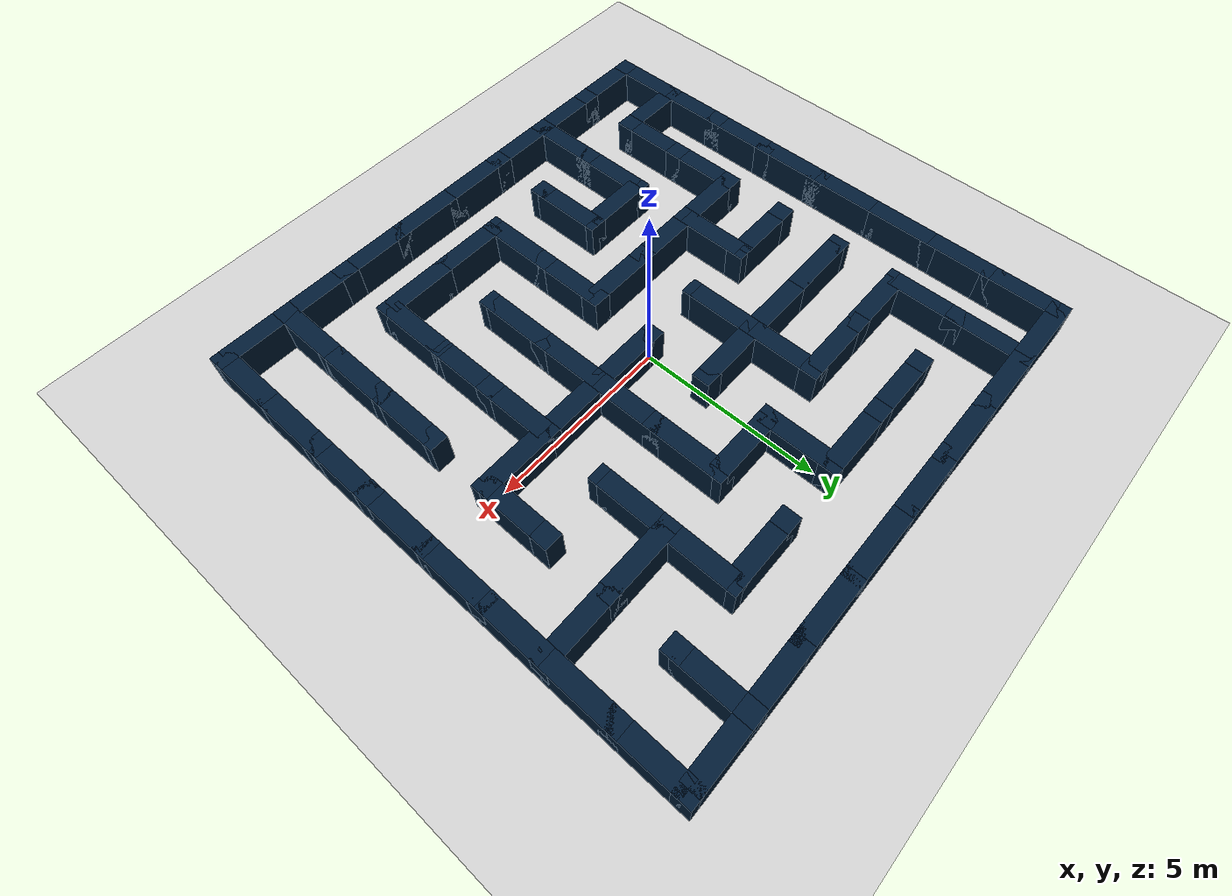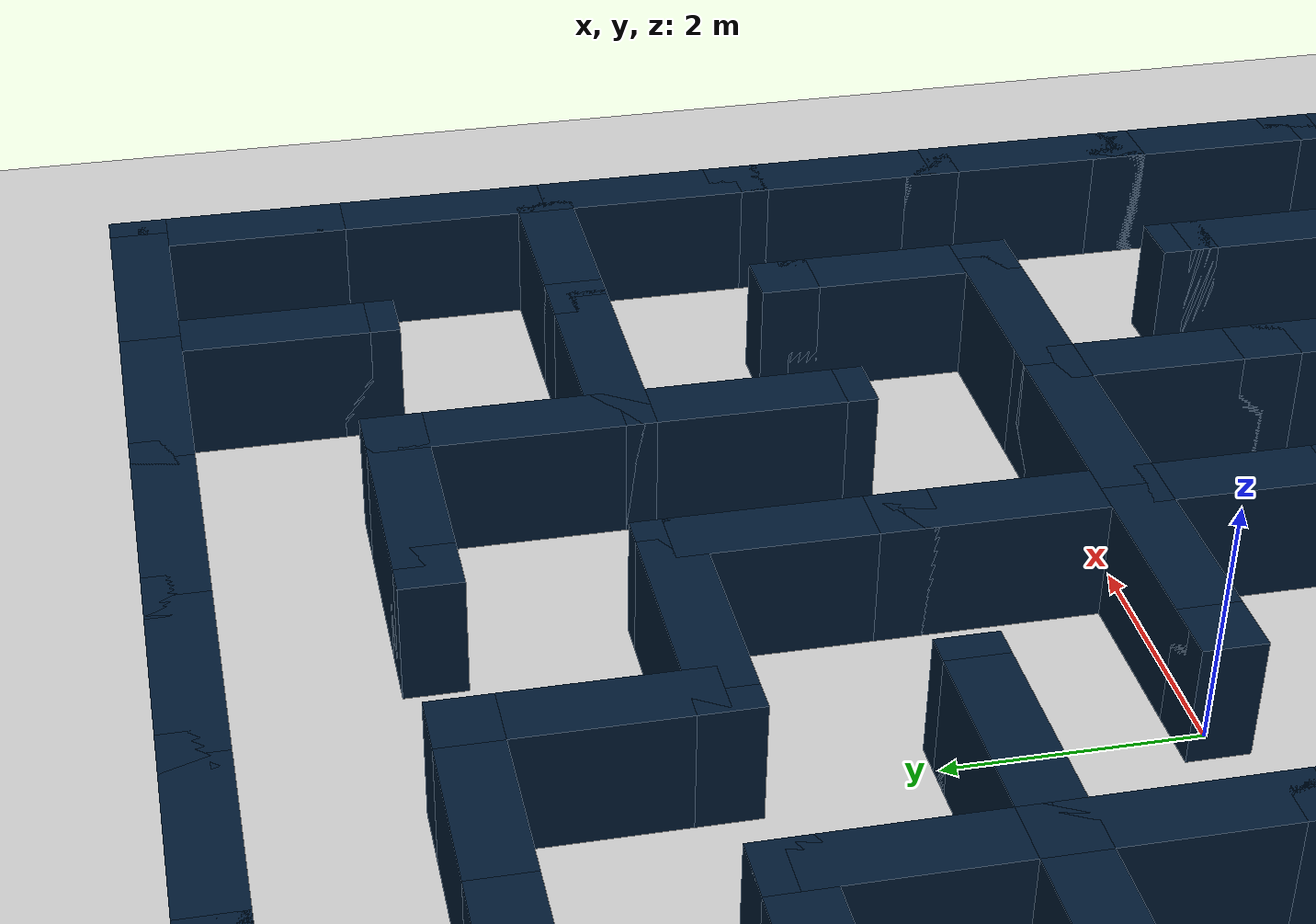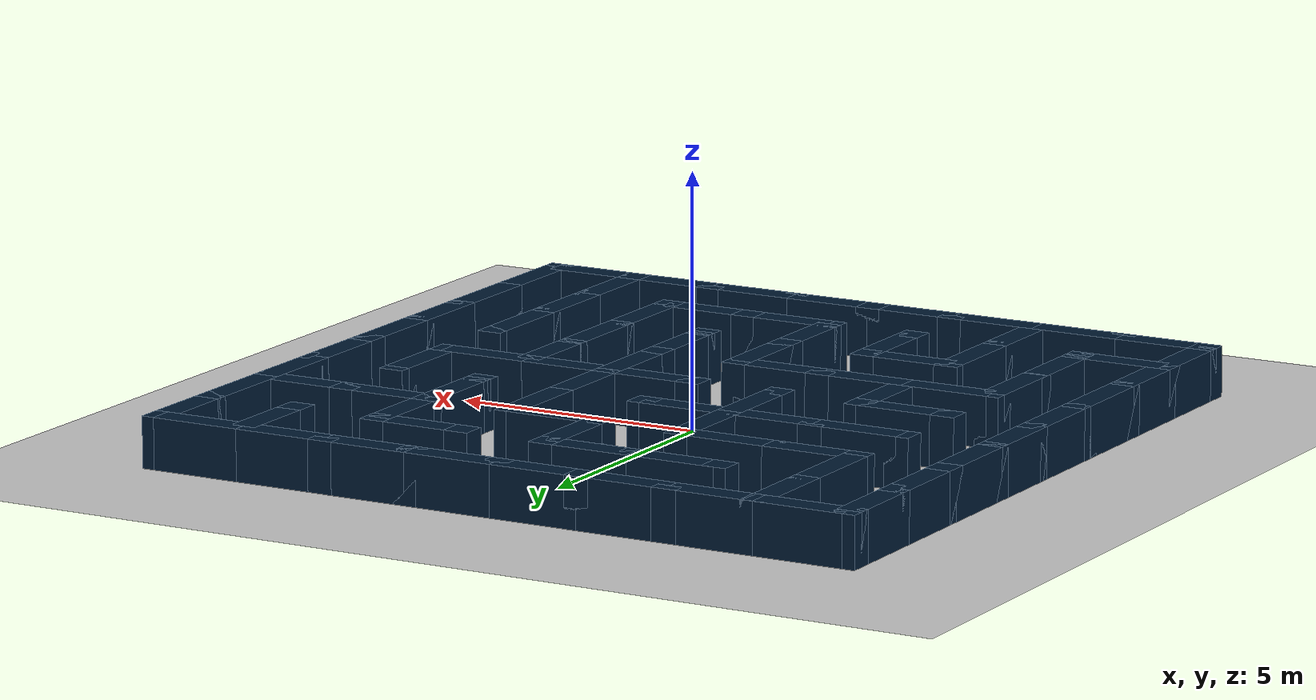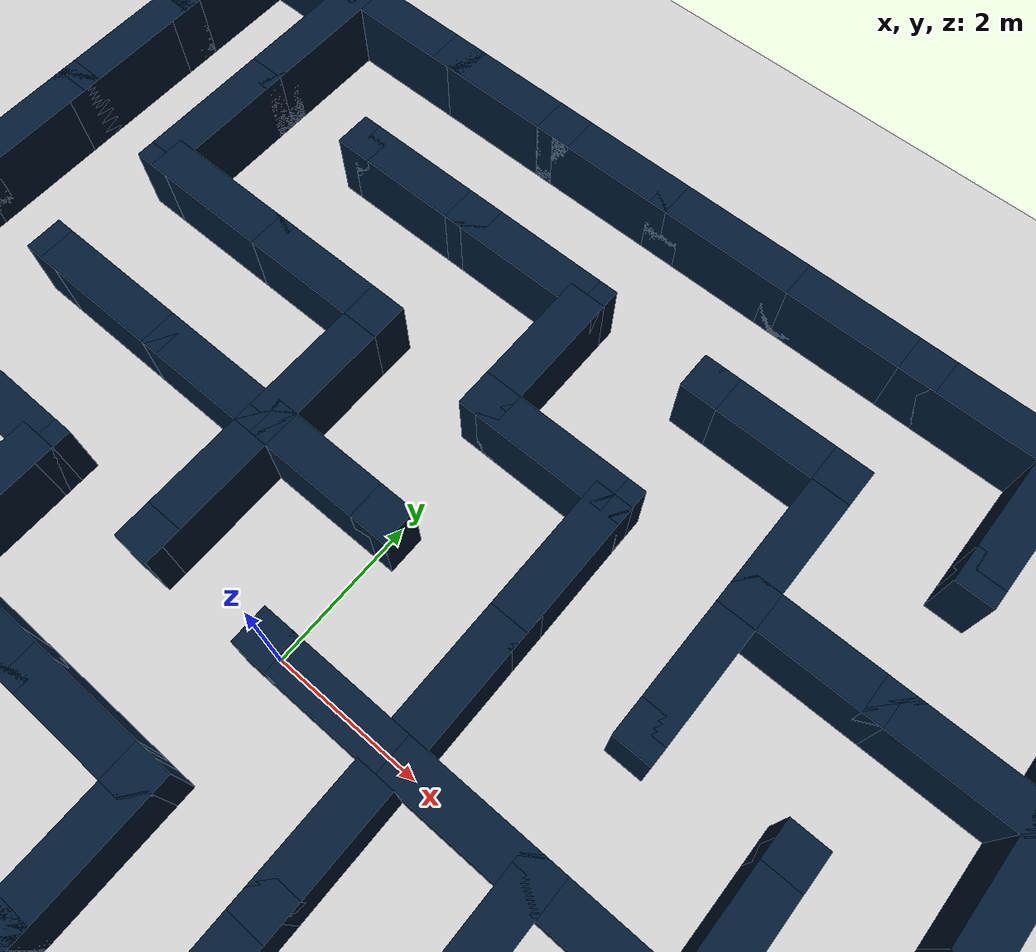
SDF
<?xml version="1.0"?>
<sdf version='1.8'>
    <world name='maze_8x8'>
        <physics name='1ms' type='ignored'>
            <max_step_size>0.003</max_step_size>
            <real_time_factor>1</real_time_factor>
            <real_time_update_rate>1000</real_time_update_rate>
        </physics>

        <!-- Plugins remain the same -->
        <plugin name="gz::sim::systems::Physics" filename="gz-sim-physics-system" />
        <plugin name="gz::sim::systems::UserCommands" filename="gz-sim-user-commands-system" />
        <plugin name="gz::sim::systems::SceneBroadcaster" filename="gz-sim-scene-broadcaster-system" />
        <plugin name="gz::sim::systems::Contact" filename="gz-sim-contact-system" />
        <plugin name="gz::sim::systems::Sensors" filename="gz-sim-sensors-system">
            <render_engine>ogre2</render_engine>
        </plugin>

        <gui fullscreen="0">
            <camera name="user_camera">
                <pose>0.0 0.0 21.60 0 1.20 0</pose>
                <view_controller>orbit</view_controller>
            </camera>
        </gui>

        <light name='sun' type='directional'>
            <cast_shadows>1</cast_shadows>
            <pose>0 0 40 0 -0 0</pose>
            <diffuse>0.8 0.8 0.8 1</diffuse>
            <specular>0.2 0.2 0.2 1</specular>
            <attenuation>
                <range>4000</range>
                <constant>0.90000000000000002</constant>
                <linear>0.01</linear>
                <quadratic>0.001</quadratic>
            </attenuation>
            <direction>-0.5 0.1 -0.9</direction>
            <spot>
                <inner_angle>0</inner_angle>
                <outer_angle>0</outer_angle>
                <falloff>0</falloff>
            </spot>
        </light>

        <gravity>0 0 -9.8</gravity>
        <magnetic_field>6e-06 2.3e-05 -4.2e-05</magnetic_field>
        <atmosphere type='adiabatic' />

        <scene>
            <ambient>0.4 0.4 0.4 1</ambient>
            <background>0.7 0.7 0.7 1</background>
            <shadows>1</shadows>
        </scene>

        <model name='ground_plane'>
            <static>1</static>
            <link name='link'>
                <collision name='collision'>
                    <geometry>
                        <plane>
                            <normal>0 0 1</normal>
                            <size>28.80 28.80</size>
                        </plane>
                    </geometry>
                    <surface>
                        <friction>
                            <ode />
                        </friction>
                        <bounce />
                        <contact />
                    </surface>
                </collision>
                <visual name='visual'>
                    <geometry>
                        <plane>
                            <normal>0 0 1</normal>
                            <size>28.80 28.80</size>
                        </plane>
                    </geometry>
                    <material>
                        <ambient>0.8 0.8 0.8 1</ambient>
                        <diffuse>0.8 0.8 0.8 1</diffuse>
                        <specular>0.8 0.8 0.8 1</specular>
                    </material>
                    <plugin name='__default__' filename='__default__' />
                </visual>
            </link>
            <plugin name='__default__' filename='__default__' />
            <pose>0 0 0 0 -0 0</pose>
        </model>

        <model name='obstacles'>
            <pose>0 0 0.50 0 0 0</pose>
            <static>true</static>
        <link name='corner_block_1'>
            <pose>-7.20 -7.20 0 0 0 0</pose>
            <static>true</static>
            <collision name='corner_block_1_collision'>
                <geometry>
                    <box>
                        <size>0.50 0.50 1.00</size>
                    </box>
                </geometry>
            </collision>
            <visual name='corner_block_1_visual'>
                <geometry>
                    <box>
                        <size>0.50 0.50 1.00</size>
                    </box>
                </geometry>
                <material>
                    <ambient>0.1 0.1 0.1 1</ambient>
                    <diffuse>0 0.1 0.2 1</diffuse>
                    <specular>0 0.01 0.05 1</specular>
                </material>
            </visual>
        </link>
        <link name='corner_block_2'>
            <pose>-5.40 -7.20 0 0 0 0</pose>
            <static>true</static>
            <collision name='corner_block_2_collision'>
                <geometry>
                    <box>
                        <size>0.50 0.50 1.00</size>
                    </box>
                </geometry>
            </collision>
            <visual name='corner_block_2_visual'>
                <geometry>
                    <box>
                        <size>0.50 0.50 1.00</size>
                    </box>
                </geometry>
                <material>
                    <ambient>0.1 0.1 0.1 1</ambient>
                    <diffuse>0 0.1 0.2 1</diffuse>
                    <specular>0 0.01 0.05 1</specular>
                </material>
            </visual>
        </link>
        <link name='corner_block_3'>
            <pose>-3.60 -7.20 0 0 0 0</pose>
            <static>true</static>
            <collision name='corner_block_3_collision'>
                <geometry>
                    <box>
                        <size>0.50 0.50 1.00</size>
                    </box>
                </geometry>
            </collision>
            <visual name='corner_block_3_visual'>
                <geometry>
                    <box>
                        <size>0.50 0.50 1.00</size>
                    </box>
                </geometry>
                <material>
                    <ambient>0.1 0.1 0.1 1</ambient>
                    <diffuse>0 0.1 0.2 1</diffuse>
                    <specular>0 0.01 0.05 1</specular>
                </material>
            </visual>
        </link>
        <link name='corner_block_4'>
            <pose>-1.80 -7.20 0 0 0 0</pose>
            <static>true</static>
            <collision name='corner_block_4_collision'>
                <geometry>
                    <box>
                        <size>0.50 0.50 1.00</size>
                    </box>
                </geometry>
            </collision>
            <visual name='corner_block_4_visual'>
                <geometry>
                    <box>
                        <size>0.50 0.50 1.00</size>
                    </box>
                </geometry>
                <material>
                    <ambient>0.1 0.1 0.1 1</ambient>
                    <diffuse>0 0.1 0.2 1</diffuse>
                    <specular>0 0.01 0.05 1</specular>
                </material>
            </visual>
        </link>
        <link name='corner_block_5'>
            <pose>0.00 -7.20 0 0 0 0</pose>
            <static>true</static>
            <collision name='corner_block_5_collision'>
                <geometry>
                    <box>
                        <size>0.50 0.50 1.00</size>
                    </box>
                </geometry>
            </collision>
            <visual name='corner_block_5_visual'>
                <geometry>
                    <box>
                        <size>0.50 0.50 1.00</size>
                    </box>
                </geometry>
                <material>
                    <ambient>0.1 0.1 0.1 1</ambient>
                    <diffuse>0 0.1 0.2 1</diffuse>
                    <specular>0 0.01 0.05 1</specular>
                </material>
            </visual>
        </link>
        <link name='corner_block_6'>
            <pose>1.80 -7.20 0 0 0 0</pose>
            <static>true</static>
            <collision name='corner_block_6_collision'>
                <geometry>
                    <box>
                        <size>0.50 0.50 1.00</size>
                    </box>
                </geometry>
            </collision>
            <visual name='corner_block_6_visual'>
                <geometry>
                    <box>
                        <size>0.50 0.50 1.00</size>
                    </box>
                </geometry>
                <material>
                    <ambient>0.1 0.1 0.1 1</ambient>
                    <diffuse>0 0.1 0.2 1</diffuse>
                    <specular>0 0.01 0.05 1</specular>
                </material>
            </visual>
        </link>
        <link name='corner_block_7'>
            <pose>3.60 -7.20 0 0 0 0</pose>
            <static>true</static>
            <collision name='corner_block_7_collision'>
                <geometry>
                    <box>
                        <size>0.50 0.50 1.00</size>
                    </box>
                </geometry>
            </collision>
            <visual name='corner_block_7_visual'>
                <geometry>
                    <box>
                        <size>0.50 0.50 1.00</size>
                    </box>
                </geometry>
                <material>
                    <ambient>0.1 0.1 0.1 1</ambient>
                    <diffuse>0 0.1 0.2 1</diffuse>
                    <specular>0 0.01 0.05 1</specular>
                </material>
            </visual>
        </link>
        <link name='corner_block_8'>
            <pose>5.40 -7.20 0 0 0 0</pose>
            <static>true</static>
            <collision name='corner_block_8_collision'>
                <geometry>
                    <box>
                        <size>0.50 0.50 1.00</size>
                    </box>
                </geometry>
            </collision>
            <visual name='corner_block_8_visual'>
                <geometry>
                    <box>
                        <size>0.50 0.50 1.00</size>
                    </box>
                </geometry>
                <material>
                    <ambient>0.1 0.1 0.1 1</ambient>
                    <diffuse>0 0.1 0.2 1</diffuse>
                    <specular>0 0.01 0.05 1</specular>
                </material>
            </visual>
        </link>
        <link name='corner_block_9'>
            <pose>7.20 -7.20 0 0 0 0</pose>
            <static>true</static>
            <collision name='corner_block_9_collision'>
                <geometry>
                    <box>
                        <size>0.50 0.50 1.00</size>
                    </box>
                </geometry>
            </collision>
            <visual name='corner_block_9_visual'>
                <geometry>
                    <box>
                        <size>0.50 0.50 1.00</size>
                    </box>
                </geometry>
                <material>
                    <ambient>0.1 0.1 0.1 1</ambient>
                    <diffuse>0 0.1 0.2 1</diffuse>
                    <specular>0 0.01 0.05 1</specular>
                </material>
            </visual>
        </link>
        <link name='corner_block_10'>
            <pose>-7.20 -5.40 0 0 0 0</pose>
            <static>true</static>
            <collision name='corner_block_10_collision'>
                <geometry>
                    <box>
                        <size>0.50 0.50 1.00</size>
                    </box>
                </geometry>
            </collision>
            <visual name='corner_block_10_visual'>
                <geometry>
                    <box>
                        <size>0.50 0.50 1.00</size>
                    </box>
                </geometry>
                <material>
                    <ambient>0.1 0.1 0.1 1</ambient>
                    <diffuse>0 0.1 0.2 1</diffuse>
                    <specular>0 0.01 0.05 1</specular>
                </material>
            </visual>
        </link>
        <link name='corner_block_11'>
            <pose>-5.40 -5.40 0 0 0 0</pose>
            <static>true</static>
            <collision name='corner_block_11_collision'>
                <geometry>
                    <box>
                        <size>0.50 0.50 1.00</size>
                    </box>
                </geometry>
            </collision>
            <visual name='corner_block_11_visual'>
                <geometry>
                    <box>
                        <size>0.50 0.50 1.00</size>
                    </box>
                </geometry>
                <material>
                    <ambient>0.1 0.1 0.1 1</ambient>
                    <diffuse>0 0.1 0.2 1</diffuse>
                    <specular>0 0.01 0.05 1</specular>
                </material>
            </visual>
        </link>
        <link name='corner_block_12'>
            <pose>-3.60 -5.40 0 0 0 0</pose>
            <static>true</static>
            <collision name='corner_block_12_collision'>
                <geometry>
                    <box>
                        <size>0.50 0.50 1.00</size>
                    </box>
                </geometry>
            </collision>
            <visual name='corner_block_12_visual'>
                <geometry>
                    <box>
                        <size>0.50 0.50 1.00</size>
                    </box>
                </geometry>
                <material>
                    <ambient>0.1 0.1 0.1 1</ambient>
                    <diffuse>0 0.1 0.2 1</diffuse>
                    <specular>0 0.01 0.05 1</specular>
                </material>
            </visual>
        </link>
        <link name='corner_block_13'>
            <pose>-1.80 -5.40 0 0 0 0</pose>
            <static>true</static>
            <collision name='corner_block_13_collision'>
                <geometry>
                    <box>
                        <size>0.50 0.50 1.00</size>
                    </box>
                </geometry>
            </collision>
            <visual name='corner_block_13_visual'>
                <geometry>
                    <box>
                        <size>0.50 0.50 1.00</size>
                    </box>
                </geometry>
                <material>
                    <ambient>0.1 0.1 0.1 1</ambient>
                    <diffuse>0 0.1 0.2 1</diffuse>
                    <specular>0 0.01 0.05 1</specular>
                </material>
            </visual>
        </link>
        <link name='corner_block_14'>
            <pose>0.00 -5.40 0 0 0 0</pose>
            <static>true</static>
            <collision name='corner_block_14_collision'>
                <geometry>
                    <box>
                        <size>0.50 0.50 1.00</size>
                    </box>
                </geometry>
            </collision>
            <visual name='corner_block_14_visual'>
                <geometry>
                    <box>
                        <size>0.50 0.50 1.00</size>
                    </box>
                </geometry>
                <material>
                    <ambient>0.1 0.1 0.1 1</ambient>
                    <diffuse>0 0.1 0.2 1</diffuse>
                    <specular>0 0.01 0.05 1</specular>
                </material>
            </visual>
        </link>
        <link name='corner_block_15'>
            <pose>1.80 -5.40 0 0 0 0</pose>
            <static>true</static>
            <collision name='corner_block_15_collision'>
                <geometry>
                    <box>
                        <size>0.50 0.50 1.00</size>
                    </box>
                </geometry>
            </collision>
            <visual name='corner_block_15_visual'>
                <geometry>
                    <box>
                        <size>0.50 0.50 1.00</size>
                    </box>
                </geometry>
                <material>
                    <ambient>0.1 0.1 0.1 1</ambient>
                    <diffuse>0 0.1 0.2 1</diffuse>
                    <specular>0 0.01 0.05 1</specular>
                </material>
            </visual>
        </link>
        <link name='corner_block_16'>
            <pose>3.60 -5.40 0 0 0 0</pose>
            <static>true</static>
            <collision name='corner_block_16_collision'>
                <geometry>
                    <box>
                        <size>0.50 0.50 1.00</size>
                    </box>
                </geometry>
            </collision>
            <visual name='corner_block_16_visual'>
                <geometry>
                    <box>
                        <size>0.50 0.50 1.00</size>
                    </box>
                </geometry>
                <material>
                    <ambient>0.1 0.1 0.1 1</ambient>
                    <diffuse>0 0.1 0.2 1</diffuse>
                    <specular>0 0.01 0.05 1</specular>
                </material>
            </visual>
        </link>
        <link name='corner_block_17'>
            <pose>5.40 -5.40 0 0 0 0</pose>
            <static>true</static>
            <collision name='corner_block_17_collision'>
                <geometry>
                    <box>
                        <size>0.50 0.50 1.00</size>
                    </box>
                </geometry>
            </collision>
            <visual name='corner_block_17_visual'>
                <geometry>
                    <box>
                        <size>0.50 0.50 1.00</size>
                    </box>
                </geometry>
                <material>
                    <ambient>0.1 0.1 0.1 1</ambient>
                    <diffuse>0 0.1 0.2 1</diffuse>
                    <specular>0 0.01 0.05 1</specular>
                </material>
            </visual>
        </link>
        <link name='corner_block_18'>
            <pose>7.20 -5.40 0 0 0 0</pose>
            <static>true</static>
            <collision name='corner_block_18_collision'>
                <geometry>
                    <box>
                        <size>0.50 0.50 1.00</size>
                    </box>
                </geometry>
            </collision>
            <visual name='corner_block_18_visual'>
                <geometry>
                    <box>
                        <size>0.50 0.50 1.00</size>
                    </box>
                </geometry>
                <material>
                    <ambient>0.1 0.1 0.1 1</ambient>
                    <diffuse>0 0.1 0.2 1</diffuse>
                    <specular>0 0.01 0.05 1</specular>
                </material>
            </visual>
        </link>
        <link name='corner_block_19'>
            <pose>-7.20 -3.60 0 0 0 0</pose>
            <static>true</static>
            <collision name='corner_block_19_collision'>
                <geometry>
                    <box>
                        <size>0.50 0.50 1.00</size>
                    </box>
                </geometry>
            </collision>
            <visual name='corner_block_19_visual'>
                <geometry>
                    <box>
                        <size>0.50 0.50 1.00</size>
                    </box>
                </geometry>
                <material>
                    <ambient>0.1 0.1 0.1 1</ambient>
                    <diffuse>0 0.1 0.2 1</diffuse>
                    <specular>0 0.01 0.05 1</specular>
                </material>
            </visual>
        </link>
        <link name='corner_block_20'>
            <pose>-5.40 -3.60 0 0 0 0</pose>
            <static>true</static>
            <collision name='corner_block_20_collision'>
                <geometry>
                    <box>
                        <size>0.50 0.50 1.00</size>
                    </box>
                </geometry>
            </collision>
            <visual name='corner_block_20_visual'>
                <geometry>
                    <box>
                        <size>0.50 0.50 1.00</size>
                    </box>
                </geometry>
                <material>
                    <ambient>0.1 0.1 0.1 1</ambient>
                    <diffuse>0 0.1 0.2 1</diffuse>
                    <specular>0 0.01 0.05 1</specular>
                </material>
            </visual>
        </link>
        <link name='corner_block_21'>
            <pose>-3.60 -3.60 0 0 0 0</pose>
            <static>true</static>
            <collision name='corner_block_21_collision'>
                <geometry>
                    <box>
                        <size>0.50 0.50 1.00</size>
                    </box>
                </geometry>
            </collision>
            <visual name='corner_block_21_visual'>
                <geometry>
                    <box>
                        <size>0.50 0.50 1.00</size>
                    </box>
                </geometry>
                <material>
                    <ambient>0.1 0.1 0.1 1</ambient>
                    <diffuse>0 0.1 0.2 1</diffuse>
                    <specular>0 0.01 0.05 1</specular>
                </material>
            </visual>
        </link>
        <link name='corner_block_22'>
            <pose>-1.80 -3.60 0 0 0 0</pose>
            <static>true</static>
            <collision name='corner_block_22_collision'>
                <geometry>
                    <box>
                        <size>0.50 0.50 1.00</size>
                    </box>
                </geometry>
            </collision>
            <visual name='corner_block_22_visual'>
                <geometry>
                    <box>
                        <size>0.50 0.50 1.00</size>
                    </box>
                </geometry>
                <material>
                    <ambient>0.1 0.1 0.1 1</ambient>
                    <diffuse>0 0.1 0.2 1</diffuse>
                    <specular>0 0.01 0.05 1</specular>
                </material>
            </visual>
        </link>
        <link name='corner_block_23'>
            <pose>0.00 -3.60 0 0 0 0</pose>
            <static>true</static>
            <collision name='corner_block_23_collision'>
                <geometry>
                    <box>
                        <size>0.50 0.50 1.00</size>
                    </box>
                </geometry>
            </collision>
            <visual name='corner_block_23_visual'>
                <geometry>
                    <box>
                        <size>0.50 0.50 1.00</size>
                    </box>
                </geometry>
                <material>
                    <ambient>0.1 0.1 0.1 1</ambient>
                    <diffuse>0 0.1 0.2 1</diffuse>
                    <specular>0 0.01 0.05 1</specular>
                </material>
            </visual>
        </link>
        <link name='corner_block_24'>
            <pose>1.80 -3.60 0 0 0 0</pose>
            <static>true</static>
            <collision name='corner_block_24_collision'>
                <geometry>
                    <box>
                        <size>0.50 0.50 1.00</size>
                    </box>
                </geometry>
            </collision>
            <visual name='corner_block_24_visual'>
                <geometry>
                    <box>
                        <size>0.50 0.50 1.00</size>
                    </box>
                </geometry>
                <material>
                    <ambient>0.1 0.1 0.1 1</ambient>
                    <diffuse>0 0.1 0.2 1</diffuse>
                    <specular>0 0.01 0.05 1</specular>
                </material>
            </visual>
        </link>
        <link name='corner_block_25'>
            <pose>3.60 -3.60 0 0 0 0</pose>
            <static>true</static>
            <collision name='corner_block_25_collision'>
                <geometry>
                    <box>
                        <size>0.50 0.50 1.00</size>
                    </box>
                </geometry>
            </collision>
            <visual name='corner_block_25_visual'>
                <geometry>
                    <box>
                        <size>0.50 0.50 1.00</size>
                    </box>
                </geometry>
                <material>
                    <ambient>0.1 0.1 0.1 1</ambient>
                    <diffuse>0 0.1 0.2 1</diffuse>
                    <specular>0 0.01 0.05 1</specular>
                </material>
            </visual>
        </link>
        <link name='corner_block_26'>
            <pose>5.40 -3.60 0 0 0 0</pose>
            <static>true</static>
            <collision name='corner_block_26_collision'>
                <geometry>
                    <box>
                        <size>0.50 0.50 1.00</size>
                    </box>
                </geometry>
            </collision>
            <visual name='corner_block_26_visual'>
                <geometry>
                    <box>
                        <size>0.50 0.50 1.00</size>
                    </box>
                </geometry>
                <material>
                    <ambient>0.1 0.1 0.1 1</ambient>
                    <diffuse>0 0.1 0.2 1</diffuse>
                    <specular>0 0.01 0.05 1</specular>
                </material>
            </visual>
        </link>
        <link name='corner_block_27'>
            <pose>7.20 -3.60 0 0 0 0</pose>
            <static>true</static>
            <collision name='corner_block_27_collision'>
                <geometry>
                    <box>
                        <size>0.50 0.50 1.00</size>
                    </box>
                </geometry>
            </collision>
            <visual name='corner_block_27_visual'>
                <geometry>
                    <box>
                        <size>0.50 0.50 1.00</size>
                    </box>
                </geometry>
                <material>
                    <ambient>0.1 0.1 0.1 1</ambient>
                    <diffuse>0 0.1 0.2 1</diffuse>
                    <specular>0 0.01 0.05 1</specular>
                </material>
            </visual>
        </link>
        <link name='corner_block_28'>
            <pose>-7.20 -1.80 0 0 0 0</pose>
            <static>true</static>
            <collision name='corner_block_28_collision'>
                <geometry>
                    <box>
                        <size>0.50 0.50 1.00</size>
                    </box>
                </geometry>
            </collision>
            <visual name='corner_block_28_visual'>
                <geometry>
                    <box>
                        <size>0.50 0.50 1.00</size>
                    </box>
                </geometry>
                <material>
                    <ambient>0.1 0.1 0.1 1</ambient>
                    <diffuse>0 0.1 0.2 1</diffuse>
                    <specular>0 0.01 0.05 1</specular>
                </material>
            </visual>
        </link>
        <link name='corner_block_29'>
            <pose>-5.40 -1.80 0 0 0 0</pose>
            <static>true</static>
            <collision name='corner_block_29_collision'>
                <geometry>
                    <box>
                        <size>0.50 0.50 1.00</size>
                    </box>
                </geometry>
            </collision>
            <visual name='corner_block_29_visual'>
                <geometry>
                    <box>
                        <size>0.50 0.50 1.00</size>
                    </box>
                </geometry>
                <material>
                    <ambient>0.1 0.1 0.1 1</ambient>
                    <diffuse>0 0.1 0.2 1</diffuse>
                    <specular>0 0.01 0.05 1</specular>
                </material>
            </visual>
        </link>
        <link name='corner_block_30'>
            <pose>-3.60 -1.80 0 0 0 0</pose>
            <static>true</static>
            <collision name='corner_block_30_collision'>
                <geometry>
                    <box>
                        <size>0.50 0.50 1.00</size>
                    </box>
                </geometry>
            </collision>
            <visual name='corner_block_30_visual'>
                <geometry>
                    <box>
                        <size>0.50 0.50 1.00</size>
                    </box>
                </geometry>
                <material>
                    <ambient>0.1 0.1 0.1 1</ambient>
                    <diffuse>0 0.1 0.2 1</diffuse>
                    <specular>0 0.01 0.05 1</specular>
                </material>
            </visual>
        </link>
        <link name='corner_block_31'>
            <pose>-1.80 -1.80 0 0 0 0</pose>
            <static>true</static>
            <collision name='corner_block_31_collision'>
                <geometry>
                    <box>
                        <size>0.50 0.50 1.00</size>
                    </box>
                </geometry>
            </collision>
            <visual name='corner_block_31_visual'>
                <geometry>
                    <box>
                        <size>0.50 0.50 1.00</size>
                    </box>
                </geometry>
                <material>
                    <ambient>0.1 0.1 0.1 1</ambient>
                    <diffuse>0 0.1 0.2 1</diffuse>
                    <specular>0 0.01 0.05 1</specular>
                </material>
            </visual>
        </link>
        <link name='corner_block_32'>
            <pose>0.00 -1.80 0 0 0 0</pose>
            <static>true</static>
            <collision name='corner_block_32_collision'>
                <geometry>
                    <box>
                        <size>0.50 0.50 1.00</size>
                    </box>
                </geometry>
            </collision>
            <visual name='corner_block_32_visual'>
                <geometry>
                    <box>
                        <size>0.50 0.50 1.00</size>
                    </box>
                </geometry>
                <material>
                    <ambient>0.1 0.1 0.1 1</ambient>
                    <diffuse>0 0.1 0.2 1</diffuse>
                    <specular>0 0.01 0.05 1</specular>
                </material>
            </visual>
        </link>
        <link name='corner_block_33'>
            <pose>1.80 -1.80 0 0 0 0</pose>
            <static>true</static>
            <collision name='corner_block_33_collision'>
                <geometry>
                    <box>
                        <size>0.50 0.50 1.00</size>
                    </box>
                </geometry>
            </collision>
            <visual name='corner_block_33_visual'>
                <geometry>
                    <box>
                        <size>0.50 0.50 1.00</size>
                    </box>
                </geometry>
                <material>
                    <ambient>0.1 0.1 0.1 1</ambient>
                    <diffuse>0 0.1 0.2 1</diffuse>
                    <specular>0 0.01 0.05 1</specular>
                </material>
            </visual>
        </link>
        <link name='corner_block_34'>
            <pose>3.60 -1.80 0 0 0 0</pose>
            <static>true</static>
            <collision name='corner_block_34_collision'>
                <geometry>
                    <box>
                        <size>0.50 0.50 1.00</size>
                    </box>
                </geometry>
            </collision>
            <visual name='corner_block_34_visual'>
                <geometry>
                    <box>
                        <size>0.50 0.50 1.00</size>
                    </box>
                </geometry>
                <material>
                    <ambient>0.1 0.1 0.1 1</ambient>
                    <diffuse>0 0.1 0.2 1</diffuse>
                    <specular>0 0.01 0.05 1</specular>
                </material>
            </visual>
        </link>
        <link name='corner_block_35'>
            <pose>5.40 -1.80 0 0 0 0</pose>
            <static>true</static>
            <collision name='corner_block_35_collision'>
                <geometry>
                    <box>
                        <size>0.50 0.50 1.00</size>
                    </box>
                </geometry>
            </collision>
            <visual name='corner_block_35_visual'>
                <geometry>
                    <box>
                        <size>0.50 0.50 1.00</size>
                    </box>
                </geometry>
                <material>
                    <ambient>0.1 0.1 0.1 1</ambient>
                    <diffuse>0 0.1 0.2 1</diffuse>
                    <specular>0 0.01 0.05 1</specular>
                </material>
            </visual>
        </link>
        <link name='corner_block_36'>
            <pose>7.20 -1.80 0 0 0 0</pose>
            <static>true</static>
            <collision name='corner_block_36_collision'>
                <geometry>
                    <box>
                        <size>0.50 0.50 1.00</size>
                    </box>
                </geometry>
            </collision>
            <visual name='corner_block_36_visual'>
                <geometry>
                    <box>
                        <size>0.50 0.50 1.00</size>
                    </box>
                </geometry>
                <material>
                    <ambient>0.1 0.1 0.1 1</ambient>
                    <diffuse>0 0.1 0.2 1</diffuse>
                    <specular>0 0.01 0.05 1</specular>
                </material>
            </visual>
        </link>
        <link name='corner_block_37'>
            <pose>-7.20 0.00 0 0 0 0</pose>
            <static>true</static>
            <collision name='corner_block_37_collision'>
                <geometry>
                    <box>
                        <size>0.50 0.50 1.00</size>
                    </box>
                </geometry>
            </collision>
            <visual name='corner_block_37_visual'>
                <geometry>
                    <box>
                        <size>0.50 0.50 1.00</size>
                    </box>
                </geometry>
                <material>
                    <ambient>0.1 0.1 0.1 1</ambient>
                    <diffuse>0 0.1 0.2 1</diffuse>
                    <specular>0 0.01 0.05 1</specular>
                </material>
            </visual>
        </link>
        <link name='corner_block_38'>
            <pose>-5.40 0.00 0 0 0 0</pose>
            <static>true</static>
            <collision name='corner_block_38_collision'>
                <geometry>
                    <box>
                        <size>0.50 0.50 1.00</size>
                    </box>
                </geometry>
            </collision>
            <visual name='corner_block_38_visual'>
                <geometry>
                    <box>
                        <size>0.50 0.50 1.00</size>
                    </box>
                </geometry>
                <material>
                    <ambient>0.1 0.1 0.1 1</ambient>
                    <diffuse>0 0.1 0.2 1</diffuse>
                    <specular>0 0.01 0.05 1</specular>
                </material>
            </visual>
        </link>
        <link name='corner_block_39'>
            <pose>-3.60 0.00 0 0 0 0</pose>
            <static>true</static>
            <collision name='corner_block_39_collision'>
                <geometry>
                    <box>
                        <size>0.50 0.50 1.00</size>
                    </box>
                </geometry>
            </collision>
            <visual name='corner_block_39_visual'>
                <geometry>
                    <box>
                        <size>0.50 0.50 1.00</size>
                    </box>
                </geometry>
                <material>
                    <ambient>0.1 0.1 0.1 1</ambient>
                    <diffuse>0 0.1 0.2 1</diffuse>
                    <specular>0 0.01 0.05 1</specular>
                </material>
            </visual>
        </link>
        <link name='corner_block_40'>
            <pose>-1.80 0.00 0 0 0 0</pose>
            <static>true</static>
            <collision name='corner_block_40_collision'>
                <geometry>
                    <box>
                        <size>0.50 0.50 1.00</size>
                    </box>
                </geometry>
            </collision>
            <visual name='corner_block_40_visual'>
                <geometry>
                    <box>
                        <size>0.50 0.50 1.00</size>
                    </box>
                </geometry>
                <material>
                    <ambient>0.1 0.1 0.1 1</ambient>
                    <diffuse>0 0.1 0.2 1</diffuse>
                    <specular>0 0.01 0.05 1</specular>
                </material>
            </visual>
        </link>
        <link name='corner_block_41'>
            <pose>0.00 0.00 0 0 0 0</pose>
            <static>true</static>
            <collision name='corner_block_41_collision'>
                <geometry>
                    <box>
                        <size>0.50 0.50 1.00</size>
                    </box>
                </geometry>
            </collision>
            <visual name='corner_block_41_visual'>
                <geometry>
                    <box>
                        <size>0.50 0.50 1.00</size>
                    </box>
                </geometry>
                <material>
                    <ambient>0.1 0.1 0.1 1</ambient>
                    <diffuse>0 0.1 0.2 1</diffuse>
                    <specular>0 0.01 0.05 1</specular>
                </material>
            </visual>
        </link>
        <link name='corner_block_42'>
            <pose>1.80 0.00 0 0 0 0</pose>
            <static>true</static>
            <collision name='corner_block_42_collision'>
                <geometry>
                    <box>
                        <size>0.50 0.50 1.00</size>
                    </box>
                </geometry>
            </collision>
            <visual name='corner_block_42_visual'>
                <geometry>
                    <box>
                        <size>0.50 0.50 1.00</size>
                    </box>
                </geometry>
                <material>
                    <ambient>0.1 0.1 0.1 1</ambient>
                    <diffuse>0 0.1 0.2 1</diffuse>
                    <specular>0 0.01 0.05 1</specular>
                </material>
            </visual>
        </link>
        <link name='corner_block_43'>
            <pose>3.60 0.00 0 0 0 0</pose>
            <static>true</static>
            <collision name='corner_block_43_collision'>
                <geometry>
                    <box>
                        <size>0.50 0.50 1.00</size>
                    </box>
                </geometry>
            </collision>
            <visual name='corner_block_43_visual'>
                <geometry>
                    <box>
                        <size>0.50 0.50 1.00</size>
                    </box>
                </geometry>
                <material>
                    <ambient>0.1 0.1 0.1 1</ambient>
                    <diffuse>0 0.1 0.2 1</diffuse>
                    <specular>0 0.01 0.05 1</specular>
                </material>
            </visual>
        </link>
        <link name='corner_block_44'>
            <pose>5.40 0.00 0 0 0 0</pose>
            <static>true</static>
            <collision name='corner_block_44_collision'>
                <geometry>
                    <box>
                        <size>0.50 0.50 1.00</size>
                    </box>
                </geometry>
            </collision>
            <visual name='corner_block_44_visual'>
                <geometry>
                    <box>
                        <size>0.50 0.50 1.00</size>
                    </box>
                </geometry>
                <material>
                    <ambient>0.1 0.1 0.1 1</ambient>
                    <diffuse>0 0.1 0.2 1</diffuse>
                    <specular>0 0.01 0.05 1</specular>
                </material>
            </visual>
        </link>
        <link name='corner_block_45'>
            <pose>7.20 0.00 0 0 0 0</pose>
            <static>true</static>
            <collision name='corner_block_45_collision'>
                <geometry>
                    <box>
                        <size>0.50 0.50 1.00</size>
                    </box>
                </geometry>
            </collision>
            <visual name='corner_block_45_visual'>
                <geometry>
                    <box>
                        <size>0.50 0.50 1.00</size>
                    </box>
                </geometry>
                <material>
                    <ambient>0.1 0.1 0.1 1</ambient>
                    <diffuse>0 0.1 0.2 1</diffuse>
                    <specular>0 0.01 0.05 1</specular>
                </material>
            </visual>
        </link>
        <link name='corner_block_46'>
            <pose>-7.20 1.80 0 0 0 0</pose>
            <static>true</static>
            <collision name='corner_block_46_collision'>
                <geometry>
                    <box>
                        <size>0.50 0.50 1.00</size>
                    </box>
                </geometry>
            </collision>
            <visual name='corner_block_46_visual'>
                <geometry>
                    <box>
                        <size>0.50 0.50 1.00</size>
                    </box>
                </geometry>
                <material>
                    <ambient>0.1 0.1 0.1 1</ambient>
                    <diffuse>0 0.1 0.2 1</diffuse>
                    <specular>0 0.01 0.05 1</specular>
                </material>
            </visual>
        </link>
        <link name='corner_block_47'>
            <pose>-5.40 1.80 0 0 0 0</pose>
            <static>true</static>
            <collision name='corner_block_47_collision'>
                <geometry>
                    <box>
                        <size>0.50 0.50 1.00</size>
                    </box>
                </geometry>
            </collision>
            <visual name='corner_block_47_visual'>
                <geometry>
                    <box>
                        <size>0.50 0.50 1.00</size>
                    </box>
                </geometry>
                <material>
                    <ambient>0.1 0.1 0.1 1</ambient>
                    <diffuse>0 0.1 0.2 1</diffuse>
                    <specular>0 0.01 0.05 1</specular>
                </material>
            </visual>
        </link>
        <link name='corner_block_48'>
            <pose>-3.60 1.80 0 0 0 0</pose>
            <static>true</static>
            <collision name='corner_block_48_collision'>
                <geometry>
                    <box>
                        <size>0.50 0.50 1.00</size>
                    </box>
                </geometry>
            </collision>
            <visual name='corner_block_48_visual'>
                <geometry>
                    <box>
                        <size>0.50 0.50 1.00</size>
                    </box>
                </geometry>
                <material>
                    <ambient>0.1 0.1 0.1 1</ambient>
                    <diffuse>0 0.1 0.2 1</diffuse>
                    <specular>0 0.01 0.05 1</specular>
                </material>
            </visual>
        </link>
        <link name='corner_block_49'>
            <pose>-1.80 1.80 0 0 0 0</pose>
            <static>true</static>
            <collision name='corner_block_49_collision'>
                <geometry>
                    <box>
                        <size>0.50 0.50 1.00</size>
                    </box>
                </geometry>
            </collision>
            <visual name='corner_block_49_visual'>
                <geometry>
                    <box>
                        <size>0.50 0.50 1.00</size>
                    </box>
                </geometry>
                <material>
                    <ambient>0.1 0.1 0.1 1</ambient>
                    <diffuse>0 0.1 0.2 1</diffuse>
                    <specular>0 0.01 0.05 1</specular>
                </material>
            </visual>
        </link>
        <link name='corner_block_50'>
            <pose>0.00 1.80 0 0 0 0</pose>
            <static>true</static>
            <collision name='corner_block_50_collision'>
                <geometry>
                    <box>
                        <size>0.50 0.50 1.00</size>
                    </box>
                </geometry>
            </collision>
            <visual name='corner_block_50_visual'>
                <geometry>
                    <box>
                        <size>0.50 0.50 1.00</size>
                    </box>
                </geometry>
                <material>
                    <ambient>0.1 0.1 0.1 1</ambient>
                    <diffuse>0 0.1 0.2 1</diffuse>
                    <specular>0 0.01 0.05 1</specular>
                </material>
            </visual>
        </link>
        <link name='corner_block_51'>
            <pose>1.80 1.80 0 0 0 0</pose>
            <static>true</static>
            <collision name='corner_block_51_collision'>
                <geometry>
                    <box>
                        <size>0.50 0.50 1.00</size>
                    </box>
                </geometry>
            </collision>
            <visual name='corner_block_51_visual'>
                <geometry>
                    <box>
                        <size>0.50 0.50 1.00</size>
                    </box>
                </geometry>
                <material>
                    <ambient>0.1 0.1 0.1 1</ambient>
                    <diffuse>0 0.1 0.2 1</diffuse>
                    <specular>0 0.01 0.05 1</specular>
                </material>
            </visual>
        </link>
        <link name='corner_block_52'>
            <pose>3.60 1.80 0 0 0 0</pose>
            <static>true</static>
            <collision name='corner_block_52_collision'>
                <geometry>
                    <box>
                        <size>0.50 0.50 1.00</size>
                    </box>
                </geometry>
            </collision>
            <visual name='corner_block_52_visual'>
                <geometry>
                    <box>
                        <size>0.50 0.50 1.00</size>
                    </box>
                </geometry>
                <material>
                    <ambient>0.1 0.1 0.1 1</ambient>
                    <diffuse>0 0.1 0.2 1</diffuse>
                    <specular>0 0.01 0.05 1</specular>
                </material>
            </visual>
        </link>
        <link name='corner_block_53'>
            <pose>5.40 1.80 0 0 0 0</pose>
            <static>true</static>
            <collision name='corner_block_53_collision'>
                <geometry>
                    <box>
                        <size>0.50 0.50 1.00</size>
                    </box>
                </geometry>
            </collision>
            <visual name='corner_block_53_visual'>
                <geometry>
                    <box>
                        <size>0.50 0.50 1.00</size>
                    </box>
                </geometry>
                <material>
                    <ambient>0.1 0.1 0.1 1</ambient>
                    <diffuse>0 0.1 0.2 1</diffuse>
                    <specular>0 0.01 0.05 1</specular>
                </material>
            </visual>
        </link>
        <link name='corner_block_54'>
            <pose>7.20 1.80 0 0 0 0</pose>
            <static>true</static>
            <collision name='corner_block_54_collision'>
                <geometry>
                    <box>
                        <size>0.50 0.50 1.00</size>
                    </box>
                </geometry>
            </collision>
            <visual name='corner_block_54_visual'>
                <geometry>
                    <box>
                        <size>0.50 0.50 1.00</size>
                    </box>
                </geometry>
                <material>
                    <ambient>0.1 0.1 0.1 1</ambient>
                    <diffuse>0 0.1 0.2 1</diffuse>
                    <specular>0 0.01 0.05 1</specular>
                </material>
            </visual>
        </link>
        <link name='corner_block_55'>
            <pose>-7.20 3.60 0 0 0 0</pose>
            <static>true</static>
            <collision name='corner_block_55_collision'>
                <geometry>
                    <box>
                        <size>0.50 0.50 1.00</size>
                    </box>
                </geometry>
            </collision>
            <visual name='corner_block_55_visual'>
                <geometry>
                    <box>
                        <size>0.50 0.50 1.00</size>
                    </box>
                </geometry>
                <material>
                    <ambient>0.1 0.1 0.1 1</ambient>
                    <diffuse>0 0.1 0.2 1</diffuse>
                    <specular>0 0.01 0.05 1</specular>
                </material>
            </visual>
        </link>
        <link name='corner_block_56'>
            <pose>-5.40 3.60 0 0 0 0</pose>
            <static>true</static>
            <collision name='corner_block_56_collision'>
                <geometry>
                    <box>
                        <size>0.50 0.50 1.00</size>
                    </box>
                </geometry>
            </collision>
            <visual name='corner_block_56_visual'>
                <geometry>
                    <box>
                        <size>0.50 0.50 1.00</size>
                    </box>
                </geometry>
                <material>
                    <ambient>0.1 0.1 0.1 1</ambient>
                    <diffuse>0 0.1 0.2 1</diffuse>
                    <specular>0 0.01 0.05 1</specular>
                </material>
            </visual>
        </link>
        <link name='corner_block_57'>
            <pose>-3.60 3.60 0 0 0 0</pose>
            <static>true</static>
            <collision name='corner_block_57_collision'>
                <geometry>
                    <box>
                        <size>0.50 0.50 1.00</size>
                    </box>
                </geometry>
            </collision>
            <visual name='corner_block_57_visual'>
                <geometry>
                    <box>
                        <size>0.50 0.50 1.00</size>
                    </box>
                </geometry>
                <material>
                    <ambient>0.1 0.1 0.1 1</ambient>
                    <diffuse>0 0.1 0.2 1</diffuse>
                    <specular>0 0.01 0.05 1</specular>
                </material>
            </visual>
        </link>
        <link name='corner_block_58'>
            <pose>-1.80 3.60 0 0 0 0</pose>
            <static>true</static>
            <collision name='corner_block_58_collision'>
                <geometry>
                    <box>
                        <size>0.50 0.50 1.00</size>
                    </box>
                </geometry>
            </collision>
            <visual name='corner_block_58_visual'>
                <geometry>
                    <box>
                        <size>0.50 0.50 1.00</size>
                    </box>
                </geometry>
                <material>
                    <ambient>0.1 0.1 0.1 1</ambient>
                    <diffuse>0 0.1 0.2 1</diffuse>
                    <specular>0 0.01 0.05 1</specular>
                </material>
            </visual>
        </link>
        <link name='corner_block_59'>
            <pose>0.00 3.60 0 0 0 0</pose>
            <static>true</static>
            <collision name='corner_block_59_collision'>
                <geometry>
                    <box>
                        <size>0.50 0.50 1.00</size>
                    </box>
                </geometry>
            </collision>
            <visual name='corner_block_59_visual'>
                <geometry>
                    <box>
                        <size>0.50 0.50 1.00</size>
                    </box>
                </geometry>
                <material>
                    <ambient>0.1 0.1 0.1 1</ambient>
                    <diffuse>0 0.1 0.2 1</diffuse>
                    <specular>0 0.01 0.05 1</specular>
                </material>
            </visual>
        </link>
        <link name='corner_block_60'>
            <pose>1.80 3.60 0 0 0 0</pose>
            <static>true</static>
            <collision name='corner_block_60_collision'>
                <geometry>
                    <box>
                        <size>0.50 0.50 1.00</size>
                    </box>
                </geometry>
            </collision>
            <visual name='corner_block_60_visual'>
                <geometry>
                    <box>
                        <size>0.50 0.50 1.00</size>
                    </box>
                </geometry>
                <material>
                    <ambient>0.1 0.1 0.1 1</ambient>
                    <diffuse>0 0.1 0.2 1</diffuse>
                    <specular>0 0.01 0.05 1</specular>
                </material>
            </visual>
        </link>
        <link name='corner_block_61'>
            <pose>3.60 3.60 0 0 0 0</pose>
            <static>true</static>
            <collision name='corner_block_61_collision'>
                <geometry>
                    <box>
                        <size>0.50 0.50 1.00</size>
                    </box>
                </geometry>
            </collision>
            <visual name='corner_block_61_visual'>
                <geometry>
                    <box>
                        <size>0.50 0.50 1.00</size>
                    </box>
                </geometry>
                <material>
                    <ambient>0.1 0.1 0.1 1</ambient>
                    <diffuse>0 0.1 0.2 1</diffuse>
                    <specular>0 0.01 0.05 1</specular>
                </material>
            </visual>
        </link>
        <link name='corner_block_62'>
            <pose>5.40 3.60 0 0 0 0</pose>
            <static>true</static>
            <collision name='corner_block_62_collision'>
                <geometry>
                    <box>
                        <size>0.50 0.50 1.00</size>
                    </box>
                </geometry>
            </collision>
            <visual name='corner_block_62_visual'>
                <geometry>
                    <box>
                        <size>0.50 0.50 1.00</size>
                    </box>
                </geometry>
                <material>
                    <ambient>0.1 0.1 0.1 1</ambient>
                    <diffuse>0 0.1 0.2 1</diffuse>
                    <specular>0 0.01 0.05 1</specular>
                </material>
            </visual>
        </link>
        <link name='corner_block_63'>
            <pose>7.20 3.60 0 0 0 0</pose>
            <static>true</static>
            <collision name='corner_block_63_collision'>
                <geometry>
                    <box>
                        <size>0.50 0.50 1.00</size>
                    </box>
                </geometry>
            </collision>
            <visual name='corner_block_63_visual'>
                <geometry>
                    <box>
                        <size>0.50 0.50 1.00</size>
                    </box>
                </geometry>
                <material>
                    <ambient>0.1 0.1 0.1 1</ambient>
                    <diffuse>0 0.1 0.2 1</diffuse>
                    <specular>0 0.01 0.05 1</specular>
                </material>
            </visual>
        </link>
        <link name='corner_block_64'>
            <pose>-7.20 5.40 0 0 0 0</pose>
            <static>true</static>
            <collision name='corner_block_64_collision'>
                <geometry>
                    <box>
                        <size>0.50 0.50 1.00</size>
                    </box>
                </geometry>
            </collision>
            <visual name='corner_block_64_visual'>
                <geometry>
                    <box>
                        <size>0.50 0.50 1.00</size>
                    </box>
                </geometry>
                <material>
                    <ambient>0.1 0.1 0.1 1</ambient>
                    <diffuse>0 0.1 0.2 1</diffuse>
                    <specular>0 0.01 0.05 1</specular>
                </material>
            </visual>
        </link>
        <link name='corner_block_65'>
            <pose>-5.40 5.40 0 0 0 0</pose>
            <static>true</static>
            <collision name='corner_block_65_collision'>
                <geometry>
                    <box>
                        <size>0.50 0.50 1.00</size>
                    </box>
                </geometry>
            </collision>
            <visual name='corner_block_65_visual'>
                <geometry>
                    <box>
                        <size>0.50 0.50 1.00</size>
                    </box>
                </geometry>
                <material>
                    <ambient>0.1 0.1 0.1 1</ambient>
                    <diffuse>0 0.1 0.2 1</diffuse>
                    <specular>0 0.01 0.05 1</specular>
                </material>
            </visual>
        </link>
        <link name='corner_block_66'>
            <pose>-3.60 5.40 0 0 0 0</pose>
            <static>true</static>
            <collision name='corner_block_66_collision'>
                <geometry>
                    <box>
                        <size>0.50 0.50 1.00</size>
                    </box>
                </geometry>
            </collision>
            <visual name='corner_block_66_visual'>
                <geometry>
                    <box>
                        <size>0.50 0.50 1.00</size>
                    </box>
                </geometry>
                <material>
                    <ambient>0.1 0.1 0.1 1</ambient>
                    <diffuse>0 0.1 0.2 1</diffuse>
                    <specular>0 0.01 0.05 1</specular>
                </material>
            </visual>
        </link>
        <link name='corner_block_67'>
            <pose>-1.80 5.40 0 0 0 0</pose>
            <static>true</static>
            <collision name='corner_block_67_collision'>
                <geometry>
                    <box>
                        <size>0.50 0.50 1.00</size>
                    </box>
                </geometry>
            </collision>
            <visual name='corner_block_67_visual'>
                <geometry>
                    <box>
                        <size>0.50 0.50 1.00</size>
                    </box>
                </geometry>
                <material>
                    <ambient>0.1 0.1 0.1 1</ambient>
                    <diffuse>0 0.1 0.2 1</diffuse>
                    <specular>0 0.01 0.05 1</specular>
                </material>
            </visual>
        </link>
        <link name='corner_block_68'>
            <pose>0.00 5.40 0 0 0 0</pose>
            <static>true</static>
            <collision name='corner_block_68_collision'>
                <geometry>
                    <box>
                        <size>0.50 0.50 1.00</size>
                    </box>
                </geometry>
            </collision>
            <visual name='corner_block_68_visual'>
                <geometry>
                    <box>
                        <size>0.50 0.50 1.00</size>
                    </box>
                </geometry>
                <material>
                    <ambient>0.1 0.1 0.1 1</ambient>
                    <diffuse>0 0.1 0.2 1</diffuse>
                    <specular>0 0.01 0.05 1</specular>
                </material>
            </visual>
        </link>
        <link name='corner_block_69'>
            <pose>1.80 5.40 0 0 0 0</pose>
            <static>true</static>
            <collision name='corner_block_69_collision'>
                <geometry>
                    <box>
                        <size>0.50 0.50 1.00</size>
                    </box>
                </geometry>
            </collision>
            <visual name='corner_block_69_visual'>
                <geometry>
                    <box>
                        <size>0.50 0.50 1.00</size>
                    </box>
                </geometry>
                <material>
                    <ambient>0.1 0.1 0.1 1</ambient>
                    <diffuse>0 0.1 0.2 1</diffuse>
                    <specular>0 0.01 0.05 1</specular>
                </material>
            </visual>
        </link>
        <link name='corner_block_70'>
            <pose>3.60 5.40 0 0 0 0</pose>
            <static>true</static>
            <collision name='corner_block_70_collision'>
                <geometry>
                    <box>
                        <size>0.50 0.50 1.00</size>
                    </box>
                </geometry>
            </collision>
            <visual name='corner_block_70_visual'>
                <geometry>
                    <box>
                        <size>0.50 0.50 1.00</size>
                    </box>
                </geometry>
                <material>
                    <ambient>0.1 0.1 0.1 1</ambient>
                    <diffuse>0 0.1 0.2 1</diffuse>
                    <specular>0 0.01 0.05 1</specular>
                </material>
            </visual>
        </link>
        <link name='corner_block_71'>
            <pose>5.40 5.40 0 0 0 0</pose>
            <static>true</static>
            <collision name='corner_block_71_collision'>
                <geometry>
                    <box>
                        <size>0.50 0.50 1.00</size>
                    </box>
                </geometry>
            </collision>
            <visual name='corner_block_71_visual'>
                <geometry>
                    <box>
                        <size>0.50 0.50 1.00</size>
                    </box>
                </geometry>
                <material>
                    <ambient>0.1 0.1 0.1 1</ambient>
                    <diffuse>0 0.1 0.2 1</diffuse>
                    <specular>0 0.01 0.05 1</specular>
                </material>
            </visual>
        </link>
        <link name='corner_block_72'>
            <pose>7.20 5.40 0 0 0 0</pose>
            <static>true</static>
            <collision name='corner_block_72_collision'>
                <geometry>
                    <box>
                        <size>0.50 0.50 1.00</size>
                    </box>
                </geometry>
            </collision>
            <visual name='corner_block_72_visual'>
                <geometry>
                    <box>
                        <size>0.50 0.50 1.00</size>
                    </box>
                </geometry>
                <material>
                    <ambient>0.1 0.1 0.1 1</ambient>
                    <diffuse>0 0.1 0.2 1</diffuse>
                    <specular>0 0.01 0.05 1</specular>
                </material>
            </visual>
        </link>
        <link name='corner_block_73'>
            <pose>-7.20 7.20 0 0 0 0</pose>
            <static>true</static>
            <collision name='corner_block_73_collision'>
                <geometry>
                    <box>
                        <size>0.50 0.50 1.00</size>
                    </box>
                </geometry>
            </collision>
            <visual name='corner_block_73_visual'>
                <geometry>
                    <box>
                        <size>0.50 0.50 1.00</size>
                    </box>
                </geometry>
                <material>
                    <ambient>0.1 0.1 0.1 1</ambient>
                    <diffuse>0 0.1 0.2 1</diffuse>
                    <specular>0 0.01 0.05 1</specular>
                </material>
            </visual>
        </link>
        <link name='corner_block_74'>
            <pose>-5.40 7.20 0 0 0 0</pose>
            <static>true</static>
            <collision name='corner_block_74_collision'>
                <geometry>
                    <box>
                        <size>0.50 0.50 1.00</size>
                    </box>
                </geometry>
            </collision>
            <visual name='corner_block_74_visual'>
                <geometry>
                    <box>
                        <size>0.50 0.50 1.00</size>
                    </box>
                </geometry>
                <material>
                    <ambient>0.1 0.1 0.1 1</ambient>
                    <diffuse>0 0.1 0.2 1</diffuse>
                    <specular>0 0.01 0.05 1</specular>
                </material>
            </visual>
        </link>
        <link name='corner_block_75'>
            <pose>-3.60 7.20 0 0 0 0</pose>
            <static>true</static>
            <collision name='corner_block_75_collision'>
                <geometry>
                    <box>
                        <size>0.50 0.50 1.00</size>
                    </box>
                </geometry>
            </collision>
            <visual name='corner_block_75_visual'>
                <geometry>
                    <box>
                        <size>0.50 0.50 1.00</size>
                    </box>
                </geometry>
                <material>
                    <ambient>0.1 0.1 0.1 1</ambient>
                    <diffuse>0 0.1 0.2 1</diffuse>
                    <specular>0 0.01 0.05 1</specular>
                </material>
            </visual>
        </link>
        <link name='corner_block_76'>
            <pose>-1.80 7.20 0 0 0 0</pose>
            <static>true</static>
            <collision name='corner_block_76_collision'>
                <geometry>
                    <box>
                        <size>0.50 0.50 1.00</size>
                    </box>
                </geometry>
            </collision>
            <visual name='corner_block_76_visual'>
                <geometry>
                    <box>
                        <size>0.50 0.50 1.00</size>
                    </box>
                </geometry>
                <material>
                    <ambient>0.1 0.1 0.1 1</ambient>
                    <diffuse>0 0.1 0.2 1</diffuse>
                    <specular>0 0.01 0.05 1</specular>
                </material>
            </visual>
        </link>
        <link name='corner_block_77'>
            <pose>0.00 7.20 0 0 0 0</pose>
            <static>true</static>
            <collision name='corner_block_77_collision'>
                <geometry>
                    <box>
                        <size>0.50 0.50 1.00</size>
                    </box>
                </geometry>
            </collision>
            <visual name='corner_block_77_visual'>
                <geometry>
                    <box>
                        <size>0.50 0.50 1.00</size>
                    </box>
                </geometry>
                <material>
                    <ambient>0.1 0.1 0.1 1</ambient>
                    <diffuse>0 0.1 0.2 1</diffuse>
                    <specular>0 0.01 0.05 1</specular>
                </material>
            </visual>
        </link>
        <link name='corner_block_78'>
            <pose>1.80 7.20 0 0 0 0</pose>
            <static>true</static>
            <collision name='corner_block_78_collision'>
                <geometry>
                    <box>
                        <size>0.50 0.50 1.00</size>
                    </box>
                </geometry>
            </collision>
            <visual name='corner_block_78_visual'>
                <geometry>
                    <box>
                        <size>0.50 0.50 1.00</size>
                    </box>
                </geometry>
                <material>
                    <ambient>0.1 0.1 0.1 1</ambient>
                    <diffuse>0 0.1 0.2 1</diffuse>
                    <specular>0 0.01 0.05 1</specular>
                </material>
            </visual>
        </link>
        <link name='corner_block_79'>
            <pose>3.60 7.20 0 0 0 0</pose>
            <static>true</static>
            <collision name='corner_block_79_collision'>
                <geometry>
                    <box>
                        <size>0.50 0.50 1.00</size>
                    </box>
                </geometry>
            </collision>
            <visual name='corner_block_79_visual'>
                <geometry>
                    <box>
                        <size>0.50 0.50 1.00</size>
                    </box>
                </geometry>
                <material>
                    <ambient>0.1 0.1 0.1 1</ambient>
                    <diffuse>0 0.1 0.2 1</diffuse>
                    <specular>0 0.01 0.05 1</specular>
                </material>
            </visual>
        </link>
        <link name='corner_block_80'>
            <pose>5.40 7.20 0 0 0 0</pose>
            <static>true</static>
            <collision name='corner_block_80_collision'>
                <geometry>
                    <box>
                        <size>0.50 0.50 1.00</size>
                    </box>
                </geometry>
            </collision>
            <visual name='corner_block_80_visual'>
                <geometry>
                    <box>
                        <size>0.50 0.50 1.00</size>
                    </box>
                </geometry>
                <material>
                    <ambient>0.1 0.1 0.1 1</ambient>
                    <diffuse>0 0.1 0.2 1</diffuse>
                    <specular>0 0.01 0.05 1</specular>
                </material>
            </visual>
        </link>
        <link name='corner_block_81'>
            <pose>7.20 7.20 0 0 0 0</pose>
            <static>true</static>
            <collision name='corner_block_81_collision'>
                <geometry>
                    <box>
                        <size>0.50 0.50 1.00</size>
                    </box>
                </geometry>
            </collision>
            <visual name='corner_block_81_visual'>
                <geometry>
                    <box>
                        <size>0.50 0.50 1.00</size>
                    </box>
                </geometry>
                <material>
                    <ambient>0.1 0.1 0.1 1</ambient>
                    <diffuse>0 0.1 0.2 1</diffuse>
                    <specular>0 0.01 0.05 1</specular>
                </material>
            </visual>
        </link>
        <link name='wall82'>
            <pose>-6.30 -7.20 0 0 0 0</pose>
            <static>true</static>
            <collision name='wall82_collision'>
                <geometry>
                    <box>
                        <size>1.80 0.50 1.00</size>
                    </box>
                </geometry>
            </collision>
            <visual name='wall82_visual'>
                <geometry>
                    <box>
                        <size>1.80 0.50 1.00</size>
                    </box>
                </geometry>
                <material>
                    <ambient>0.1 0.1 0.1 1</ambient>
                    <diffuse>0 0.1 0.2 1</diffuse>
                    <specular>0 0.01 0.05 1</specular>
                </material>
            </visual>
        </link>
        <link name='wall83'>
            <pose>-4.50 -7.20 0 0 0 0</pose>
            <static>true</static>
            <collision name='wall83_collision'>
                <geometry>
                    <box>
                        <size>1.80 0.50 1.00</size>
                    </box>
                </geometry>
            </collision>
            <visual name='wall83_visual'>
                <geometry>
                    <box>
                        <size>1.80 0.50 1.00</size>
                    </box>
                </geometry>
                <material>
                    <ambient>0.1 0.1 0.1 1</ambient>
                    <diffuse>0 0.1 0.2 1</diffuse>
                    <specular>0 0.01 0.05 1</specular>
                </material>
            </visual>
        </link>
        <link name='wall84'>
            <pose>-2.70 -7.20 0 0 0 0</pose>
            <static>true</static>
            <collision name='wall84_collision'>
                <geometry>
                    <box>
                        <size>1.80 0.50 1.00</size>
                    </box>
                </geometry>
            </collision>
            <visual name='wall84_visual'>
                <geometry>
                    <box>
                        <size>1.80 0.50 1.00</size>
                    </box>
                </geometry>
                <material>
                    <ambient>0.1 0.1 0.1 1</ambient>
                    <diffuse>0 0.1 0.2 1</diffuse>
                    <specular>0 0.01 0.05 1</specular>
                </material>
            </visual>
        </link>
        <link name='wall85'>
            <pose>-0.90 -7.20 0 0 0 0</pose>
            <static>true</static>
            <collision name='wall85_collision'>
                <geometry>
                    <box>
                        <size>1.80 0.50 1.00</size>
                    </box>
                </geometry>
            </collision>
            <visual name='wall85_visual'>
                <geometry>
                    <box>
                        <size>1.80 0.50 1.00</size>
                    </box>
                </geometry>
                <material>
                    <ambient>0.1 0.1 0.1 1</ambient>
                    <diffuse>0 0.1 0.2 1</diffuse>
                    <specular>0 0.01 0.05 1</specular>
                </material>
            </visual>
        </link>
        <link name='wall86'>
            <pose>0.90 -7.20 0 0 0 0</pose>
            <static>true</static>
            <collision name='wall86_collision'>
                <geometry>
                    <box>
                        <size>1.80 0.50 1.00</size>
                    </box>
                </geometry>
            </collision>
            <visual name='wall86_visual'>
                <geometry>
                    <box>
                        <size>1.80 0.50 1.00</size>
                    </box>
                </geometry>
                <material>
                    <ambient>0.1 0.1 0.1 1</ambient>
                    <diffuse>0 0.1 0.2 1</diffuse>
                    <specular>0 0.01 0.05 1</specular>
                </material>
            </visual>
        </link>
        <link name='wall87'>
            <pose>2.70 -7.20 0 0 0 0</pose>
            <static>true</static>
            <collision name='wall87_collision'>
                <geometry>
                    <box>
                        <size>1.80 0.50 1.00</size>
                    </box>
                </geometry>
            </collision>
            <visual name='wall87_visual'>
                <geometry>
                    <box>
                        <size>1.80 0.50 1.00</size>
                    </box>
                </geometry>
                <material>
                    <ambient>0.1 0.1 0.1 1</ambient>
                    <diffuse>0 0.1 0.2 1</diffuse>
                    <specular>0 0.01 0.05 1</specular>
                </material>
            </visual>
        </link>
        <link name='wall88'>
            <pose>4.50 -7.20 0 0 0 0</pose>
            <static>true</static>
            <collision name='wall88_collision'>
                <geometry>
                    <box>
                        <size>1.80 0.50 1.00</size>
                    </box>
                </geometry>
            </collision>
            <visual name='wall88_visual'>
                <geometry>
                    <box>
                        <size>1.80 0.50 1.00</size>
                    </box>
                </geometry>
                <material>
                    <ambient>0.1 0.1 0.1 1</ambient>
                    <diffuse>0 0.1 0.2 1</diffuse>
                    <specular>0 0.01 0.05 1</specular>
                </material>
            </visual>
        </link>
        <link name='wall89'>
            <pose>6.30 -7.20 0 0 0 0</pose>
            <static>true</static>
            <collision name='wall89_collision'>
                <geometry>
                    <box>
                        <size>1.80 0.50 1.00</size>
                    </box>
                </geometry>
            </collision>
            <visual name='wall89_visual'>
                <geometry>
                    <box>
                        <size>1.80 0.50 1.00</size>
                    </box>
                </geometry>
                <material>
                    <ambient>0.1 0.1 0.1 1</ambient>
                    <diffuse>0 0.1 0.2 1</diffuse>
                    <specular>0 0.01 0.05 1</specular>
                </material>
            </visual>
        </link>
        <link name='wall90'>
            <pose>-6.30 -5.40 0 0 0 0</pose>
            <static>true</static>
            <collision name='wall90_collision'>
                <geometry>
                    <box>
                        <size>1.80 0.50 1.00</size>
                    </box>
                </geometry>
            </collision>
            <visual name='wall90_visual'>
                <geometry>
                    <box>
                        <size>1.80 0.50 1.00</size>
                    </box>
                </geometry>
                <material>
                    <ambient>0.1 0.1 0.1 1</ambient>
                    <diffuse>0 0.1 0.2 1</diffuse>
                    <specular>0 0.01 0.05 1</specular>
                </material>
            </visual>
        </link>
        <link name='wall91'>
            <pose>0.90 -5.40 0 0 0 0</pose>
            <static>true</static>
            <collision name='wall91_collision'>
                <geometry>
                    <box>
                        <size>1.80 0.50 1.00</size>
                    </box>
                </geometry>
            </collision>
            <visual name='wall91_visual'>
                <geometry>
                    <box>
                        <size>1.80 0.50 1.00</size>
                    </box>
                </geometry>
                <material>
                    <ambient>0.1 0.1 0.1 1</ambient>
                    <diffuse>0 0.1 0.2 1</diffuse>
                    <specular>0 0.01 0.05 1</specular>
                </material>
            </visual>
        </link>
        <link name='wall92'>
            <pose>2.70 -5.40 0 0 0 0</pose>
            <static>true</static>
            <collision name='wall92_collision'>
                <geometry>
                    <box>
                        <size>1.80 0.50 1.00</size>
                    </box>
                </geometry>
            </collision>
            <visual name='wall92_visual'>
                <geometry>
                    <box>
                        <size>1.80 0.50 1.00</size>
                    </box>
                </geometry>
                <material>
                    <ambient>0.1 0.1 0.1 1</ambient>
                    <diffuse>0 0.1 0.2 1</diffuse>
                    <specular>0 0.01 0.05 1</specular>
                </material>
            </visual>
        </link>
        <link name='wall93'>
            <pose>-2.70 -3.60 0 0 0 0</pose>
            <static>true</static>
            <collision name='wall93_collision'>
                <geometry>
                    <box>
                        <size>1.80 0.50 1.00</size>
                    </box>
                </geometry>
            </collision>
            <visual name='wall93_visual'>
                <geometry>
                    <box>
                        <size>1.80 0.50 1.00</size>
                    </box>
                </geometry>
                <material>
                    <ambient>0.1 0.1 0.1 1</ambient>
                    <diffuse>0 0.1 0.2 1</diffuse>
                    <specular>0 0.01 0.05 1</specular>
                </material>
            </visual>
        </link>
        <link name='wall94'>
            <pose>-4.50 -1.80 0 0 0 0</pose>
            <static>true</static>
            <collision name='wall94_collision'>
                <geometry>
                    <box>
                        <size>1.80 0.50 1.00</size>
                    </box>
                </geometry>
            </collision>
            <visual name='wall94_visual'>
                <geometry>
                    <box>
                        <size>1.80 0.50 1.00</size>
                    </box>
                </geometry>
                <material>
                    <ambient>0.1 0.1 0.1 1</ambient>
                    <diffuse>0 0.1 0.2 1</diffuse>
                    <specular>0 0.01 0.05 1</specular>
                </material>
            </visual>
        </link>
        <link name='wall95'>
            <pose>-2.70 -1.80 0 0 0 0</pose>
            <static>true</static>
            <collision name='wall95_collision'>
                <geometry>
                    <box>
                        <size>1.80 0.50 1.00</size>
                    </box>
                </geometry>
            </collision>
            <visual name='wall95_visual'>
                <geometry>
                    <box>
                        <size>1.80 0.50 1.00</size>
                    </box>
                </geometry>
                <material>
                    <ambient>0.1 0.1 0.1 1</ambient>
                    <diffuse>0 0.1 0.2 1</diffuse>
                    <specular>0 0.01 0.05 1</specular>
                </material>
            </visual>
        </link>
        <link name='wall96'>
            <pose>-0.90 -1.80 0 0 0 0</pose>
            <static>true</static>
            <collision name='wall96_collision'>
                <geometry>
                    <box>
                        <size>1.80 0.50 1.00</size>
                    </box>
                </geometry>
            </collision>
            <visual name='wall96_visual'>
                <geometry>
                    <box>
                        <size>1.80 0.50 1.00</size>
                    </box>
                </geometry>
                <material>
                    <ambient>0.1 0.1 0.1 1</ambient>
                    <diffuse>0 0.1 0.2 1</diffuse>
                    <specular>0 0.01 0.05 1</specular>
                </material>
            </visual>
        </link>
        <link name='wall97'>
            <pose>-4.50 0.00 0 0 0 0</pose>
            <static>true</static>
            <collision name='wall97_collision'>
                <geometry>
                    <box>
                        <size>1.80 0.50 1.00</size>
                    </box>
                </geometry>
            </collision>
            <visual name='wall97_visual'>
                <geometry>
                    <box>
                        <size>1.80 0.50 1.00</size>
                    </box>
                </geometry>
                <material>
                    <ambient>0.1 0.1 0.1 1</ambient>
                    <diffuse>0 0.1 0.2 1</diffuse>
                    <specular>0 0.01 0.05 1</specular>
                </material>
            </visual>
        </link>
        <link name='wall98'>
            <pose>0.90 0.00 0 0 0 0</pose>
            <static>true</static>
            <collision name='wall98_collision'>
                <geometry>
                    <box>
                        <size>1.80 0.50 1.00</size>
                    </box>
                </geometry>
            </collision>
            <visual name='wall98_visual'>
                <geometry>
                    <box>
                        <size>1.80 0.50 1.00</size>
                    </box>
                </geometry>
                <material>
                    <ambient>0.1 0.1 0.1 1</ambient>
                    <diffuse>0 0.1 0.2 1</diffuse>
                    <specular>0 0.01 0.05 1</specular>
                </material>
            </visual>
        </link>
        <link name='wall99'>
            <pose>2.70 0.00 0 0 0 0</pose>
            <static>true</static>
            <collision name='wall99_collision'>
                <geometry>
                    <box>
                        <size>1.80 0.50 1.00</size>
                    </box>
                </geometry>
            </collision>
            <visual name='wall99_visual'>
                <geometry>
                    <box>
                        <size>1.80 0.50 1.00</size>
                    </box>
                </geometry>
                <material>
                    <ambient>0.1 0.1 0.1 1</ambient>
                    <diffuse>0 0.1 0.2 1</diffuse>
                    <specular>0 0.01 0.05 1</specular>
                </material>
            </visual>
        </link>
        <link name='wall100'>
            <pose>4.50 0.00 0 0 0 0</pose>
            <static>true</static>
            <collision name='wall100_collision'>
                <geometry>
                    <box>
                        <size>1.80 0.50 1.00</size>
                    </box>
                </geometry>
            </collision>
            <visual name='wall100_visual'>
                <geometry>
                    <box>
                        <size>1.80 0.50 1.00</size>
                    </box>
                </geometry>
                <material>
                    <ambient>0.1 0.1 0.1 1</ambient>
                    <diffuse>0 0.1 0.2 1</diffuse>
                    <specular>0 0.01 0.05 1</specular>
                </material>
            </visual>
        </link>
        <link name='wall101'>
            <pose>-4.50 1.80 0 0 0 0</pose>
            <static>true</static>
            <collision name='wall101_collision'>
                <geometry>
                    <box>
                        <size>1.80 0.50 1.00</size>
                    </box>
                </geometry>
            </collision>
            <visual name='wall101_visual'>
                <geometry>
                    <box>
                        <size>1.80 0.50 1.00</size>
                    </box>
                </geometry>
                <material>
                    <ambient>0.1 0.1 0.1 1</ambient>
                    <diffuse>0 0.1 0.2 1</diffuse>
                    <specular>0 0.01 0.05 1</specular>
                </material>
            </visual>
        </link>
        <link name='wall102'>
            <pose>-2.70 1.80 0 0 0 0</pose>
            <static>true</static>
            <collision name='wall102_collision'>
                <geometry>
                    <box>
                        <size>1.80 0.50 1.00</size>
                    </box>
                </geometry>
            </collision>
            <visual name='wall102_visual'>
                <geometry>
                    <box>
                        <size>1.80 0.50 1.00</size>
                    </box>
                </geometry>
                <material>
                    <ambient>0.1 0.1 0.1 1</ambient>
                    <diffuse>0 0.1 0.2 1</diffuse>
                    <specular>0 0.01 0.05 1</specular>
                </material>
            </visual>
        </link>
        <link name='wall103'>
            <pose>-0.90 1.80 0 0 0 0</pose>
            <static>true</static>
            <collision name='wall103_collision'>
                <geometry>
                    <box>
                        <size>1.80 0.50 1.00</size>
                    </box>
                </geometry>
            </collision>
            <visual name='wall103_visual'>
                <geometry>
                    <box>
                        <size>1.80 0.50 1.00</size>
                    </box>
                </geometry>
                <material>
                    <ambient>0.1 0.1 0.1 1</ambient>
                    <diffuse>0 0.1 0.2 1</diffuse>
                    <specular>0 0.01 0.05 1</specular>
                </material>
            </visual>
        </link>
        <link name='wall104'>
            <pose>-4.50 3.60 0 0 0 0</pose>
            <static>true</static>
            <collision name='wall104_collision'>
                <geometry>
                    <box>
                        <size>1.80 0.50 1.00</size>
                    </box>
                </geometry>
            </collision>
            <visual name='wall104_visual'>
                <geometry>
                    <box>
                        <size>1.80 0.50 1.00</size>
                    </box>
                </geometry>
                <material>
                    <ambient>0.1 0.1 0.1 1</ambient>
                    <diffuse>0 0.1 0.2 1</diffuse>
                    <specular>0 0.01 0.05 1</specular>
                </material>
            </visual>
        </link>
        <link name='wall105'>
            <pose>-2.70 3.60 0 0 0 0</pose>
            <static>true</static>
            <collision name='wall105_collision'>
                <geometry>
                    <box>
                        <size>1.80 0.50 1.00</size>
                    </box>
                </geometry>
            </collision>
            <visual name='wall105_visual'>
                <geometry>
                    <box>
                        <size>1.80 0.50 1.00</size>
                    </box>
                </geometry>
                <material>
                    <ambient>0.1 0.1 0.1 1</ambient>
                    <diffuse>0 0.1 0.2 1</diffuse>
                    <specular>0 0.01 0.05 1</specular>
                </material>
            </visual>
        </link>
        <link name='wall106'>
            <pose>0.90 3.60 0 0 0 0</pose>
            <static>true</static>
            <collision name='wall106_collision'>
                <geometry>
                    <box>
                        <size>1.80 0.50 1.00</size>
                    </box>
                </geometry>
            </collision>
            <visual name='wall106_visual'>
                <geometry>
                    <box>
                        <size>1.80 0.50 1.00</size>
                    </box>
                </geometry>
                <material>
                    <ambient>0.1 0.1 0.1 1</ambient>
                    <diffuse>0 0.1 0.2 1</diffuse>
                    <specular>0 0.01 0.05 1</specular>
                </material>
            </visual>
        </link>
        <link name='wall107'>
            <pose>4.50 3.60 0 0 0 0</pose>
            <static>true</static>
            <collision name='wall107_collision'>
                <geometry>
                    <box>
                        <size>1.80 0.50 1.00</size>
                    </box>
                </geometry>
            </collision>
            <visual name='wall107_visual'>
                <geometry>
                    <box>
                        <size>1.80 0.50 1.00</size>
                    </box>
                </geometry>
                <material>
                    <ambient>0.1 0.1 0.1 1</ambient>
                    <diffuse>0 0.1 0.2 1</diffuse>
                    <specular>0 0.01 0.05 1</specular>
                </material>
            </visual>
        </link>
        <link name='wall108'>
            <pose>6.30 3.60 0 0 0 0</pose>
            <static>true</static>
            <collision name='wall108_collision'>
                <geometry>
                    <box>
                        <size>1.80 0.50 1.00</size>
                    </box>
                </geometry>
            </collision>
            <visual name='wall108_visual'>
                <geometry>
                    <box>
                        <size>1.80 0.50 1.00</size>
                    </box>
                </geometry>
                <material>
                    <ambient>0.1 0.1 0.1 1</ambient>
                    <diffuse>0 0.1 0.2 1</diffuse>
                    <specular>0 0.01 0.05 1</specular>
                </material>
            </visual>
        </link>
        <link name='wall109'>
            <pose>-2.70 5.40 0 0 0 0</pose>
            <static>true</static>
            <collision name='wall109_collision'>
                <geometry>
                    <box>
                        <size>1.80 0.50 1.00</size>
                    </box>
                </geometry>
            </collision>
            <visual name='wall109_visual'>
                <geometry>
                    <box>
                        <size>1.80 0.50 1.00</size>
                    </box>
                </geometry>
                <material>
                    <ambient>0.1 0.1 0.1 1</ambient>
                    <diffuse>0 0.1 0.2 1</diffuse>
                    <specular>0 0.01 0.05 1</specular>
                </material>
            </visual>
        </link>
        <link name='wall110'>
            <pose>-0.90 5.40 0 0 0 0</pose>
            <static>true</static>
            <collision name='wall110_collision'>
                <geometry>
                    <box>
                        <size>1.80 0.50 1.00</size>
                    </box>
                </geometry>
            </collision>
            <visual name='wall110_visual'>
                <geometry>
                    <box>
                        <size>1.80 0.50 1.00</size>
                    </box>
                </geometry>
                <material>
                    <ambient>0.1 0.1 0.1 1</ambient>
                    <diffuse>0 0.1 0.2 1</diffuse>
                    <specular>0 0.01 0.05 1</specular>
                </material>
            </visual>
        </link>
        <link name='wall111'>
            <pose>2.70 5.40 0 0 0 0</pose>
            <static>true</static>
            <collision name='wall111_collision'>
                <geometry>
                    <box>
                        <size>1.80 0.50 1.00</size>
                    </box>
                </geometry>
            </collision>
            <visual name='wall111_visual'>
                <geometry>
                    <box>
                        <size>1.80 0.50 1.00</size>
                    </box>
                </geometry>
                <material>
                    <ambient>0.1 0.1 0.1 1</ambient>
                    <diffuse>0 0.1 0.2 1</diffuse>
                    <specular>0 0.01 0.05 1</specular>
                </material>
            </visual>
        </link>
        <link name='wall112'>
            <pose>-6.30 7.20 0 0 0 0</pose>
            <static>true</static>
            <collision name='wall112_collision'>
                <geometry>
                    <box>
                        <size>1.80 0.50 1.00</size>
                    </box>
                </geometry>
            </collision>
            <visual name='wall112_visual'>
                <geometry>
                    <box>
                        <size>1.80 0.50 1.00</size>
                    </box>
                </geometry>
                <material>
                    <ambient>0.1 0.1 0.1 1</ambient>
                    <diffuse>0 0.1 0.2 1</diffuse>
                    <specular>0 0.01 0.05 1</specular>
                </material>
            </visual>
        </link>
        <link name='wall113'>
            <pose>-4.50 7.20 0 0 0 0</pose>
            <static>true</static>
            <collision name='wall113_collision'>
                <geometry>
                    <box>
                        <size>1.80 0.50 1.00</size>
                    </box>
                </geometry>
            </collision>
            <visual name='wall113_visual'>
                <geometry>
                    <box>
                        <size>1.80 0.50 1.00</size>
                    </box>
                </geometry>
                <material>
                    <ambient>0.1 0.1 0.1 1</ambient>
                    <diffuse>0 0.1 0.2 1</diffuse>
                    <specular>0 0.01 0.05 1</specular>
                </material>
            </visual>
        </link>
        <link name='wall114'>
            <pose>-2.70 7.20 0 0 0 0</pose>
            <static>true</static>
            <collision name='wall114_collision'>
                <geometry>
                    <box>
                        <size>1.80 0.50 1.00</size>
                    </box>
                </geometry>
            </collision>
            <visual name='wall114_visual'>
                <geometry>
                    <box>
                        <size>1.80 0.50 1.00</size>
                    </box>
                </geometry>
                <material>
                    <ambient>0.1 0.1 0.1 1</ambient>
                    <diffuse>0 0.1 0.2 1</diffuse>
                    <specular>0 0.01 0.05 1</specular>
                </material>
            </visual>
        </link>
        <link name='wall115'>
            <pose>-0.90 7.20 0 0 0 0</pose>
            <static>true</static>
            <collision name='wall115_collision'>
                <geometry>
                    <box>
                        <size>1.80 0.50 1.00</size>
                    </box>
                </geometry>
            </collision>
            <visual name='wall115_visual'>
                <geometry>
                    <box>
                        <size>1.80 0.50 1.00</size>
                    </box>
                </geometry>
                <material>
                    <ambient>0.1 0.1 0.1 1</ambient>
                    <diffuse>0 0.1 0.2 1</diffuse>
                    <specular>0 0.01 0.05 1</specular>
                </material>
            </visual>
        </link>
        <link name='wall116'>
            <pose>0.90 7.20 0 0 0 0</pose>
            <static>true</static>
            <collision name='wall116_collision'>
                <geometry>
                    <box>
                        <size>1.80 0.50 1.00</size>
                    </box>
                </geometry>
            </collision>
            <visual name='wall116_visual'>
                <geometry>
                    <box>
                        <size>1.80 0.50 1.00</size>
                    </box>
                </geometry>
                <material>
                    <ambient>0.1 0.1 0.1 1</ambient>
                    <diffuse>0 0.1 0.2 1</diffuse>
                    <specular>0 0.01 0.05 1</specular>
                </material>
            </visual>
        </link>
        <link name='wall117'>
            <pose>2.70 7.20 0 0 0 0</pose>
            <static>true</static>
            <collision name='wall117_collision'>
                <geometry>
                    <box>
                        <size>1.80 0.50 1.00</size>
                    </box>
                </geometry>
            </collision>
            <visual name='wall117_visual'>
                <geometry>
                    <box>
                        <size>1.80 0.50 1.00</size>
                    </box>
                </geometry>
                <material>
                    <ambient>0.1 0.1 0.1 1</ambient>
                    <diffuse>0 0.1 0.2 1</diffuse>
                    <specular>0 0.01 0.05 1</specular>
                </material>
            </visual>
        </link>
        <link name='wall118'>
            <pose>4.50 7.20 0 0 0 0</pose>
            <static>true</static>
            <collision name='wall118_collision'>
                <geometry>
                    <box>
                        <size>1.80 0.50 1.00</size>
                    </box>
                </geometry>
            </collision>
            <visual name='wall118_visual'>
                <geometry>
                    <box>
                        <size>1.80 0.50 1.00</size>
                    </box>
                </geometry>
                <material>
                    <ambient>0.1 0.1 0.1 1</ambient>
                    <diffuse>0 0.1 0.2 1</diffuse>
                    <specular>0 0.01 0.05 1</specular>
                </material>
            </visual>
        </link>
        <link name='wall119'>
            <pose>6.30 7.20 0 0 0 0</pose>
            <static>true</static>
            <collision name='wall119_collision'>
                <geometry>
                    <box>
                        <size>1.80 0.50 1.00</size>
                    </box>
                </geometry>
            </collision>
            <visual name='wall119_visual'>
                <geometry>
                    <box>
                        <size>1.80 0.50 1.00</size>
                    </box>
                </geometry>
                <material>
                    <ambient>0.1 0.1 0.1 1</ambient>
                    <diffuse>0 0.1 0.2 1</diffuse>
                    <specular>0 0.01 0.05 1</specular>
                </material>
            </visual>
        </link>
        <link name='wall120'>
            <pose>-7.20 -6.30 0 0 0 0</pose>
            <static>true</static>
            <collision name='wall120_collision'>
                <geometry>
                    <box>
                        <size>0.50 1.80 1.00</size>
                    </box>
                </geometry>
            </collision>
            <visual name='wall120_visual'>
                <geometry>
                    <box>
                        <size>0.50 1.80 1.00</size>
                    </box>
                </geometry>
                <material>
                    <ambient>0.1 0.1 0.1 1</ambient>
                    <diffuse>0 0.1 0.2 1</diffuse>
                    <specular>0 0.01 0.05 1</specular>
                </material>
            </visual>
        </link>
        <link name='wall121'>
            <pose>-3.60 -6.30 0 0 0 0</pose>
            <static>true</static>
            <collision name='wall121_collision'>
                <geometry>
                    <box>
                        <size>0.50 1.80 1.00</size>
                    </box>
                </geometry>
            </collision>
            <visual name='wall121_visual'>
                <geometry>
                    <box>
                        <size>0.50 1.80 1.00</size>
                    </box>
                </geometry>
                <material>
                    <ambient>0.1 0.1 0.1 1</ambient>
                    <diffuse>0 0.1 0.2 1</diffuse>
                    <specular>0 0.01 0.05 1</specular>
                </material>
            </visual>
        </link>
        <link name='wall122'>
            <pose>5.40 -6.30 0 0 0 0</pose>
            <static>true</static>
            <collision name='wall122_collision'>
                <geometry>
                    <box>
                        <size>0.50 1.80 1.00</size>
                    </box>
                </geometry>
            </collision>
            <visual name='wall122_visual'>
                <geometry>
                    <box>
                        <size>0.50 1.80 1.00</size>
                    </box>
                </geometry>
                <material>
                    <ambient>0.1 0.1 0.1 1</ambient>
                    <diffuse>0 0.1 0.2 1</diffuse>
                    <specular>0 0.01 0.05 1</specular>
                </material>
            </visual>
        </link>
        <link name='wall123'>
            <pose>7.20 -6.30 0 0 0 0</pose>
            <static>true</static>
            <collision name='wall123_collision'>
                <geometry>
                    <box>
                        <size>0.50 1.80 1.00</size>
                    </box>
                </geometry>
            </collision>
            <visual name='wall123_visual'>
                <geometry>
                    <box>
                        <size>0.50 1.80 1.00</size>
                    </box>
                </geometry>
                <material>
                    <ambient>0.1 0.1 0.1 1</ambient>
                    <diffuse>0 0.1 0.2 1</diffuse>
                    <specular>0 0.01 0.05 1</specular>
                </material>
            </visual>
        </link>
        <link name='wall124'>
            <pose>-7.20 -4.50 0 0 0 0</pose>
            <static>true</static>
            <collision name='wall124_collision'>
                <geometry>
                    <box>
                        <size>0.50 1.80 1.00</size>
                    </box>
                </geometry>
            </collision>
            <visual name='wall124_visual'>
                <geometry>
                    <box>
                        <size>0.50 1.80 1.00</size>
                    </box>
                </geometry>
                <material>
                    <ambient>0.1 0.1 0.1 1</ambient>
                    <diffuse>0 0.1 0.2 1</diffuse>
                    <specular>0 0.01 0.05 1</specular>
                </material>
            </visual>
        </link>
        <link name='wall125'>
            <pose>-5.40 -4.50 0 0 0 0</pose>
            <static>true</static>
            <collision name='wall125_collision'>
                <geometry>
                    <box>
                        <size>0.50 1.80 1.00</size>
                    </box>
                </geometry>
            </collision>
            <visual name='wall125_visual'>
                <geometry>
                    <box>
                        <size>0.50 1.80 1.00</size>
                    </box>
                </geometry>
                <material>
                    <ambient>0.1 0.1 0.1 1</ambient>
                    <diffuse>0 0.1 0.2 1</diffuse>
                    <specular>0 0.01 0.05 1</specular>
                </material>
            </visual>
        </link>
        <link name='wall126'>
            <pose>-3.60 -4.50 0 0 0 0</pose>
            <static>true</static>
            <collision name='wall126_collision'>
                <geometry>
                    <box>
                        <size>0.50 1.80 1.00</size>
                    </box>
                </geometry>
            </collision>
            <visual name='wall126_visual'>
                <geometry>
                    <box>
                        <size>0.50 1.80 1.00</size>
                    </box>
                </geometry>
                <material>
                    <ambient>0.1 0.1 0.1 1</ambient>
                    <diffuse>0 0.1 0.2 1</diffuse>
                    <specular>0 0.01 0.05 1</specular>
                </material>
            </visual>
        </link>
        <link name='wall127'>
            <pose>-1.80 -4.50 0 0 0 0</pose>
            <static>true</static>
            <collision name='wall127_collision'>
                <geometry>
                    <box>
                        <size>0.50 1.80 1.00</size>
                    </box>
                </geometry>
            </collision>
            <visual name='wall127_visual'>
                <geometry>
                    <box>
                        <size>0.50 1.80 1.00</size>
                    </box>
                </geometry>
                <material>
                    <ambient>0.1 0.1 0.1 1</ambient>
                    <diffuse>0 0.1 0.2 1</diffuse>
                    <specular>0 0.01 0.05 1</specular>
                </material>
            </visual>
        </link>
        <link name='wall128'>
            <pose>0.00 -4.50 0 0 0 0</pose>
            <static>true</static>
            <collision name='wall128_collision'>
                <geometry>
                    <box>
                        <size>0.50 1.80 1.00</size>
                    </box>
                </geometry>
            </collision>
            <visual name='wall128_visual'>
                <geometry>
                    <box>
                        <size>0.50 1.80 1.00</size>
                    </box>
                </geometry>
                <material>
                    <ambient>0.1 0.1 0.1 1</ambient>
                    <diffuse>0 0.1 0.2 1</diffuse>
                    <specular>0 0.01 0.05 1</specular>
                </material>
            </visual>
        </link>
        <link name='wall129'>
            <pose>3.60 -4.50 0 0 0 0</pose>
            <static>true</static>
            <collision name='wall129_collision'>
                <geometry>
                    <box>
                        <size>0.50 1.80 1.00</size>
                    </box>
                </geometry>
            </collision>
            <visual name='wall129_visual'>
                <geometry>
                    <box>
                        <size>0.50 1.80 1.00</size>
                    </box>
                </geometry>
                <material>
                    <ambient>0.1 0.1 0.1 1</ambient>
                    <diffuse>0 0.1 0.2 1</diffuse>
                    <specular>0 0.01 0.05 1</specular>
                </material>
            </visual>
        </link>
        <link name='wall130'>
            <pose>5.40 -4.50 0 0 0 0</pose>
            <static>true</static>
            <collision name='wall130_collision'>
                <geometry>
                    <box>
                        <size>0.50 1.80 1.00</size>
                    </box>
                </geometry>
            </collision>
            <visual name='wall130_visual'>
                <geometry>
                    <box>
                        <size>0.50 1.80 1.00</size>
                    </box>
                </geometry>
                <material>
                    <ambient>0.1 0.1 0.1 1</ambient>
                    <diffuse>0 0.1 0.2 1</diffuse>
                    <specular>0 0.01 0.05 1</specular>
                </material>
            </visual>
        </link>
        <link name='wall131'>
            <pose>7.20 -4.50 0 0 0 0</pose>
            <static>true</static>
            <collision name='wall131_collision'>
                <geometry>
                    <box>
                        <size>0.50 1.80 1.00</size>
                    </box>
                </geometry>
            </collision>
            <visual name='wall131_visual'>
                <geometry>
                    <box>
                        <size>0.50 1.80 1.00</size>
                    </box>
                </geometry>
                <material>
                    <ambient>0.1 0.1 0.1 1</ambient>
                    <diffuse>0 0.1 0.2 1</diffuse>
                    <specular>0 0.01 0.05 1</specular>
                </material>
            </visual>
        </link>
        <link name='wall132'>
            <pose>-7.20 -2.70 0 0 0 0</pose>
            <static>true</static>
            <collision name='wall132_collision'>
                <geometry>
                    <box>
                        <size>0.50 1.80 1.00</size>
                    </box>
                </geometry>
            </collision>
            <visual name='wall132_visual'>
                <geometry>
                    <box>
                        <size>0.50 1.80 1.00</size>
                    </box>
                </geometry>
                <material>
                    <ambient>0.1 0.1 0.1 1</ambient>
                    <diffuse>0 0.1 0.2 1</diffuse>
                    <specular>0 0.01 0.05 1</specular>
                </material>
            </visual>
        </link>
        <link name='wall133'>
            <pose>-5.40 -2.70 0 0 0 0</pose>
            <static>true</static>
            <collision name='wall133_collision'>
                <geometry>
                    <box>
                        <size>0.50 1.80 1.00</size>
                    </box>
                </geometry>
            </collision>
            <visual name='wall133_visual'>
                <geometry>
                    <box>
                        <size>0.50 1.80 1.00</size>
                    </box>
                </geometry>
                <material>
                    <ambient>0.1 0.1 0.1 1</ambient>
                    <diffuse>0 0.1 0.2 1</diffuse>
                    <specular>0 0.01 0.05 1</specular>
                </material>
            </visual>
        </link>
        <link name='wall134'>
            <pose>0.00 -2.70 0 0 0 0</pose>
            <static>true</static>
            <collision name='wall134_collision'>
                <geometry>
                    <box>
                        <size>0.50 1.80 1.00</size>
                    </box>
                </geometry>
            </collision>
            <visual name='wall134_visual'>
                <geometry>
                    <box>
                        <size>0.50 1.80 1.00</size>
                    </box>
                </geometry>
                <material>
                    <ambient>0.1 0.1 0.1 1</ambient>
                    <diffuse>0 0.1 0.2 1</diffuse>
                    <specular>0 0.01 0.05 1</specular>
                </material>
            </visual>
        </link>
        <link name='wall135'>
            <pose>1.80 -2.70 0 0 0 0</pose>
            <static>true</static>
            <collision name='wall135_collision'>
                <geometry>
                    <box>
                        <size>0.50 1.80 1.00</size>
                    </box>
                </geometry>
            </collision>
            <visual name='wall135_visual'>
                <geometry>
                    <box>
                        <size>0.50 1.80 1.00</size>
                    </box>
                </geometry>
                <material>
                    <ambient>0.1 0.1 0.1 1</ambient>
                    <diffuse>0 0.1 0.2 1</diffuse>
                    <specular>0 0.01 0.05 1</specular>
                </material>
            </visual>
        </link>
        <link name='wall136'>
            <pose>3.60 -2.70 0 0 0 0</pose>
            <static>true</static>
            <collision name='wall136_collision'>
                <geometry>
                    <box>
                        <size>0.50 1.80 1.00</size>
                    </box>
                </geometry>
            </collision>
            <visual name='wall136_visual'>
                <geometry>
                    <box>
                        <size>0.50 1.80 1.00</size>
                    </box>
                </geometry>
                <material>
                    <ambient>0.1 0.1 0.1 1</ambient>
                    <diffuse>0 0.1 0.2 1</diffuse>
                    <specular>0 0.01 0.05 1</specular>
                </material>
            </visual>
        </link>
        <link name='wall137'>
            <pose>5.40 -2.70 0 0 0 0</pose>
            <static>true</static>
            <collision name='wall137_collision'>
                <geometry>
                    <box>
                        <size>0.50 1.80 1.00</size>
                    </box>
                </geometry>
            </collision>
            <visual name='wall137_visual'>
                <geometry>
                    <box>
                        <size>0.50 1.80 1.00</size>
                    </box>
                </geometry>
                <material>
                    <ambient>0.1 0.1 0.1 1</ambient>
                    <diffuse>0 0.1 0.2 1</diffuse>
                    <specular>0 0.01 0.05 1</specular>
                </material>
            </visual>
        </link>
        <link name='wall138'>
            <pose>7.20 -2.70 0 0 0 0</pose>
            <static>true</static>
            <collision name='wall138_collision'>
                <geometry>
                    <box>
                        <size>0.50 1.80 1.00</size>
                    </box>
                </geometry>
            </collision>
            <visual name='wall138_visual'>
                <geometry>
                    <box>
                        <size>0.50 1.80 1.00</size>
                    </box>
                </geometry>
                <material>
                    <ambient>0.1 0.1 0.1 1</ambient>
                    <diffuse>0 0.1 0.2 1</diffuse>
                    <specular>0 0.01 0.05 1</specular>
                </material>
            </visual>
        </link>
        <link name='wall139'>
            <pose>-7.20 -0.90 0 0 0 0</pose>
            <static>true</static>
            <collision name='wall139_collision'>
                <geometry>
                    <box>
                        <size>0.50 1.80 1.00</size>
                    </box>
                </geometry>
            </collision>
            <visual name='wall139_visual'>
                <geometry>
                    <box>
                        <size>0.50 1.80 1.00</size>
                    </box>
                </geometry>
                <material>
                    <ambient>0.1 0.1 0.1 1</ambient>
                    <diffuse>0 0.1 0.2 1</diffuse>
                    <specular>0 0.01 0.05 1</specular>
                </material>
            </visual>
        </link>
        <link name='wall140'>
            <pose>-3.60 -0.90 0 0 0 0</pose>
            <static>true</static>
            <collision name='wall140_collision'>
                <geometry>
                    <box>
                        <size>0.50 1.80 1.00</size>
                    </box>
                </geometry>
            </collision>
            <visual name='wall140_visual'>
                <geometry>
                    <box>
                        <size>0.50 1.80 1.00</size>
                    </box>
                </geometry>
                <material>
                    <ambient>0.1 0.1 0.1 1</ambient>
                    <diffuse>0 0.1 0.2 1</diffuse>
                    <specular>0 0.01 0.05 1</specular>
                </material>
            </visual>
        </link>
        <link name='wall141'>
            <pose>1.80 -0.90 0 0 0 0</pose>
            <static>true</static>
            <collision name='wall141_collision'>
                <geometry>
                    <box>
                        <size>0.50 1.80 1.00</size>
                    </box>
                </geometry>
            </collision>
            <visual name='wall141_visual'>
                <geometry>
                    <box>
                        <size>0.50 1.80 1.00</size>
                    </box>
                </geometry>
                <material>
                    <ambient>0.1 0.1 0.1 1</ambient>
                    <diffuse>0 0.1 0.2 1</diffuse>
                    <specular>0 0.01 0.05 1</specular>
                </material>
            </visual>
        </link>
        <link name='wall142'>
            <pose>3.60 -0.90 0 0 0 0</pose>
            <static>true</static>
            <collision name='wall142_collision'>
                <geometry>
                    <box>
                        <size>0.50 1.80 1.00</size>
                    </box>
                </geometry>
            </collision>
            <visual name='wall142_visual'>
                <geometry>
                    <box>
                        <size>0.50 1.80 1.00</size>
                    </box>
                </geometry>
                <material>
                    <ambient>0.1 0.1 0.1 1</ambient>
                    <diffuse>0 0.1 0.2 1</diffuse>
                    <specular>0 0.01 0.05 1</specular>
                </material>
            </visual>
        </link>
        <link name='wall143'>
            <pose>7.20 -0.90 0 0 0 0</pose>
            <static>true</static>
            <collision name='wall143_collision'>
                <geometry>
                    <box>
                        <size>0.50 1.80 1.00</size>
                    </box>
                </geometry>
            </collision>
            <visual name='wall143_visual'>
                <geometry>
                    <box>
                        <size>0.50 1.80 1.00</size>
                    </box>
                </geometry>
                <material>
                    <ambient>0.1 0.1 0.1 1</ambient>
                    <diffuse>0 0.1 0.2 1</diffuse>
                    <specular>0 0.01 0.05 1</specular>
                </material>
            </visual>
        </link>
        <link name='wall144'>
            <pose>-7.20 0.90 0 0 0 0</pose>
            <static>true</static>
            <collision name='wall144_collision'>
                <geometry>
                    <box>
                        <size>0.50 1.80 1.00</size>
                    </box>
                </geometry>
            </collision>
            <visual name='wall144_visual'>
                <geometry>
                    <box>
                        <size>0.50 1.80 1.00</size>
                    </box>
                </geometry>
                <material>
                    <ambient>0.1 0.1 0.1 1</ambient>
                    <diffuse>0 0.1 0.2 1</diffuse>
                    <specular>0 0.01 0.05 1</specular>
                </material>
            </visual>
        </link>
        <link name='wall145'>
            <pose>-1.80 0.90 0 0 0 0</pose>
            <static>true</static>
            <collision name='wall145_collision'>
                <geometry>
                    <box>
                        <size>0.50 1.80 1.00</size>
                    </box>
                </geometry>
            </collision>
            <visual name='wall145_visual'>
                <geometry>
                    <box>
                        <size>0.50 1.80 1.00</size>
                    </box>
                </geometry>
                <material>
                    <ambient>0.1 0.1 0.1 1</ambient>
                    <diffuse>0 0.1 0.2 1</diffuse>
                    <specular>0 0.01 0.05 1</specular>
                </material>
            </visual>
        </link>
        <link name='wall146'>
            <pose>1.80 0.90 0 0 0 0</pose>
            <static>true</static>
            <collision name='wall146_collision'>
                <geometry>
                    <box>
                        <size>0.50 1.80 1.00</size>
                    </box>
                </geometry>
            </collision>
            <visual name='wall146_visual'>
                <geometry>
                    <box>
                        <size>0.50 1.80 1.00</size>
                    </box>
                </geometry>
                <material>
                    <ambient>0.1 0.1 0.1 1</ambient>
                    <diffuse>0 0.1 0.2 1</diffuse>
                    <specular>0 0.01 0.05 1</specular>
                </material>
            </visual>
        </link>
        <link name='wall147'>
            <pose>5.40 0.90 0 0 0 0</pose>
            <static>true</static>
            <collision name='wall147_collision'>
                <geometry>
                    <box>
                        <size>0.50 1.80 1.00</size>
                    </box>
                </geometry>
            </collision>
            <visual name='wall147_visual'>
                <geometry>
                    <box>
                        <size>0.50 1.80 1.00</size>
                    </box>
                </geometry>
                <material>
                    <ambient>0.1 0.1 0.1 1</ambient>
                    <diffuse>0 0.1 0.2 1</diffuse>
                    <specular>0 0.01 0.05 1</specular>
                </material>
            </visual>
        </link>
        <link name='wall148'>
            <pose>7.20 0.90 0 0 0 0</pose>
            <static>true</static>
            <collision name='wall148_collision'>
                <geometry>
                    <box>
                        <size>0.50 1.80 1.00</size>
                    </box>
                </geometry>
            </collision>
            <visual name='wall148_visual'>
                <geometry>
                    <box>
                        <size>0.50 1.80 1.00</size>
                    </box>
                </geometry>
                <material>
                    <ambient>0.1 0.1 0.1 1</ambient>
                    <diffuse>0 0.1 0.2 1</diffuse>
                    <specular>0 0.01 0.05 1</specular>
                </material>
            </visual>
        </link>
        <link name='wall149'>
            <pose>-7.20 2.70 0 0 0 0</pose>
            <static>true</static>
            <collision name='wall149_collision'>
                <geometry>
                    <box>
                        <size>0.50 1.80 1.00</size>
                    </box>
                </geometry>
            </collision>
            <visual name='wall149_visual'>
                <geometry>
                    <box>
                        <size>0.50 1.80 1.00</size>
                    </box>
                </geometry>
                <material>
                    <ambient>0.1 0.1 0.1 1</ambient>
                    <diffuse>0 0.1 0.2 1</diffuse>
                    <specular>0 0.01 0.05 1</specular>
                </material>
            </visual>
        </link>
        <link name='wall150'>
            <pose>-1.80 2.70 0 0 0 0</pose>
            <static>true</static>
            <collision name='wall150_collision'>
                <geometry>
                    <box>
                        <size>0.50 1.80 1.00</size>
                    </box>
                </geometry>
            </collision>
            <visual name='wall150_visual'>
                <geometry>
                    <box>
                        <size>0.50 1.80 1.00</size>
                    </box>
                </geometry>
                <material>
                    <ambient>0.1 0.1 0.1 1</ambient>
                    <diffuse>0 0.1 0.2 1</diffuse>
                    <specular>0 0.01 0.05 1</specular>
                </material>
            </visual>
        </link>
        <link name='wall151'>
            <pose>1.80 2.70 0 0 0 0</pose>
            <static>true</static>
            <collision name='wall151_collision'>
                <geometry>
                    <box>
                        <size>0.50 1.80 1.00</size>
                    </box>
                </geometry>
            </collision>
            <visual name='wall151_visual'>
                <geometry>
                    <box>
                        <size>0.50 1.80 1.00</size>
                    </box>
                </geometry>
                <material>
                    <ambient>0.1 0.1 0.1 1</ambient>
                    <diffuse>0 0.1 0.2 1</diffuse>
                    <specular>0 0.01 0.05 1</specular>
                </material>
            </visual>
        </link>
        <link name='wall152'>
            <pose>3.60 2.70 0 0 0 0</pose>
            <static>true</static>
            <collision name='wall152_collision'>
                <geometry>
                    <box>
                        <size>0.50 1.80 1.00</size>
                    </box>
                </geometry>
            </collision>
            <visual name='wall152_visual'>
                <geometry>
                    <box>
                        <size>0.50 1.80 1.00</size>
                    </box>
                </geometry>
                <material>
                    <ambient>0.1 0.1 0.1 1</ambient>
                    <diffuse>0 0.1 0.2 1</diffuse>
                    <specular>0 0.01 0.05 1</specular>
                </material>
            </visual>
        </link>
        <link name='wall153'>
            <pose>7.20 2.70 0 0 0 0</pose>
            <static>true</static>
            <collision name='wall153_collision'>
                <geometry>
                    <box>
                        <size>0.50 1.80 1.00</size>
                    </box>
                </geometry>
            </collision>
            <visual name='wall153_visual'>
                <geometry>
                    <box>
                        <size>0.50 1.80 1.00</size>
                    </box>
                </geometry>
                <material>
                    <ambient>0.1 0.1 0.1 1</ambient>
                    <diffuse>0 0.1 0.2 1</diffuse>
                    <specular>0 0.01 0.05 1</specular>
                </material>
            </visual>
        </link>
        <link name='wall154'>
            <pose>-7.20 4.50 0 0 0 0</pose>
            <static>true</static>
            <collision name='wall154_collision'>
                <geometry>
                    <box>
                        <size>0.50 1.80 1.00</size>
                    </box>
                </geometry>
            </collision>
            <visual name='wall154_visual'>
                <geometry>
                    <box>
                        <size>0.50 1.80 1.00</size>
                    </box>
                </geometry>
                <material>
                    <ambient>0.1 0.1 0.1 1</ambient>
                    <diffuse>0 0.1 0.2 1</diffuse>
                    <specular>0 0.01 0.05 1</specular>
                </material>
            </visual>
        </link>
        <link name='wall155'>
            <pose>-5.40 4.50 0 0 0 0</pose>
            <static>true</static>
            <collision name='wall155_collision'>
                <geometry>
                    <box>
                        <size>0.50 1.80 1.00</size>
                    </box>
                </geometry>
            </collision>
            <visual name='wall155_visual'>
                <geometry>
                    <box>
                        <size>0.50 1.80 1.00</size>
                    </box>
                </geometry>
                <material>
                    <ambient>0.1 0.1 0.1 1</ambient>
                    <diffuse>0 0.1 0.2 1</diffuse>
                    <specular>0 0.01 0.05 1</specular>
                </material>
            </visual>
        </link>
        <link name='wall156'>
            <pose>0.00 4.50 0 0 0 0</pose>
            <static>true</static>
            <collision name='wall156_collision'>
                <geometry>
                    <box>
                        <size>0.50 1.80 1.00</size>
                    </box>
                </geometry>
            </collision>
            <visual name='wall156_visual'>
                <geometry>
                    <box>
                        <size>0.50 1.80 1.00</size>
                    </box>
                </geometry>
                <material>
                    <ambient>0.1 0.1 0.1 1</ambient>
                    <diffuse>0 0.1 0.2 1</diffuse>
                    <specular>0 0.01 0.05 1</specular>
                </material>
            </visual>
        </link>
        <link name='wall157'>
            <pose>3.60 4.50 0 0 0 0</pose>
            <static>true</static>
            <collision name='wall157_collision'>
                <geometry>
                    <box>
                        <size>0.50 1.80 1.00</size>
                    </box>
                </geometry>
            </collision>
            <visual name='wall157_visual'>
                <geometry>
                    <box>
                        <size>0.50 1.80 1.00</size>
                    </box>
                </geometry>
                <material>
                    <ambient>0.1 0.1 0.1 1</ambient>
                    <diffuse>0 0.1 0.2 1</diffuse>
                    <specular>0 0.01 0.05 1</specular>
                </material>
            </visual>
        </link>
        <link name='wall158'>
            <pose>7.20 4.50 0 0 0 0</pose>
            <static>true</static>
            <collision name='wall158_collision'>
                <geometry>
                    <box>
                        <size>0.50 1.80 1.00</size>
                    </box>
                </geometry>
            </collision>
            <visual name='wall158_visual'>
                <geometry>
                    <box>
                        <size>0.50 1.80 1.00</size>
                    </box>
                </geometry>
                <material>
                    <ambient>0.1 0.1 0.1 1</ambient>
                    <diffuse>0 0.1 0.2 1</diffuse>
                    <specular>0 0.01 0.05 1</specular>
                </material>
            </visual>
        </link>
        <link name='wall159'>
            <pose>-7.20 6.30 0 0 0 0</pose>
            <static>true</static>
            <collision name='wall159_collision'>
                <geometry>
                    <box>
                        <size>0.50 1.80 1.00</size>
                    </box>
                </geometry>
            </collision>
            <visual name='wall159_visual'>
                <geometry>
                    <box>
                        <size>0.50 1.80 1.00</size>
                    </box>
                </geometry>
                <material>
                    <ambient>0.1 0.1 0.1 1</ambient>
                    <diffuse>0 0.1 0.2 1</diffuse>
                    <specular>0 0.01 0.05 1</specular>
                </material>
            </visual>
        </link>
        <link name='wall160'>
            <pose>-5.40 6.30 0 0 0 0</pose>
            <static>true</static>
            <collision name='wall160_collision'>
                <geometry>
                    <box>
                        <size>0.50 1.80 1.00</size>
                    </box>
                </geometry>
            </collision>
            <visual name='wall160_visual'>
                <geometry>
                    <box>
                        <size>0.50 1.80 1.00</size>
                    </box>
                </geometry>
                <material>
                    <ambient>0.1 0.1 0.1 1</ambient>
                    <diffuse>0 0.1 0.2 1</diffuse>
                    <specular>0 0.01 0.05 1</specular>
                </material>
            </visual>
        </link>
        <link name='wall161'>
            <pose>5.40 6.30 0 0 0 0</pose>
            <static>true</static>
            <collision name='wall161_collision'>
                <geometry>
                    <box>
                        <size>0.50 1.80 1.00</size>
                    </box>
                </geometry>
            </collision>
            <visual name='wall161_visual'>
                <geometry>
                    <box>
                        <size>0.50 1.80 1.00</size>
                    </box>
                </geometry>
                <material>
                    <ambient>0.1 0.1 0.1 1</ambient>
                    <diffuse>0 0.1 0.2 1</diffuse>
                    <specular>0 0.01 0.05 1</specular>
                </material>
            </visual>
        </link>
        <link name='wall162'>
            <pose>7.20 6.30 0 0 0 0</pose>
            <static>true</static>
            <collision name='wall162_collision'>
                <geometry>
                    <box>
                        <size>0.50 1.80 1.00</size>
                    </box>
                </geometry>
            </collision>
            <visual name='wall162_visual'>
                <geometry>
                    <box>
                        <size>0.50 1.80 1.00</size>
                    </box>
                </geometry>
                <material>
                    <ambient>0.1 0.1 0.1 1</ambient>
                    <diffuse>0 0.1 0.2 1</diffuse>
                    <specular>0 0.01 0.05 1</specular>
                </material>
            </visual>
        </link>
    </model>
</world>
</sdf>
